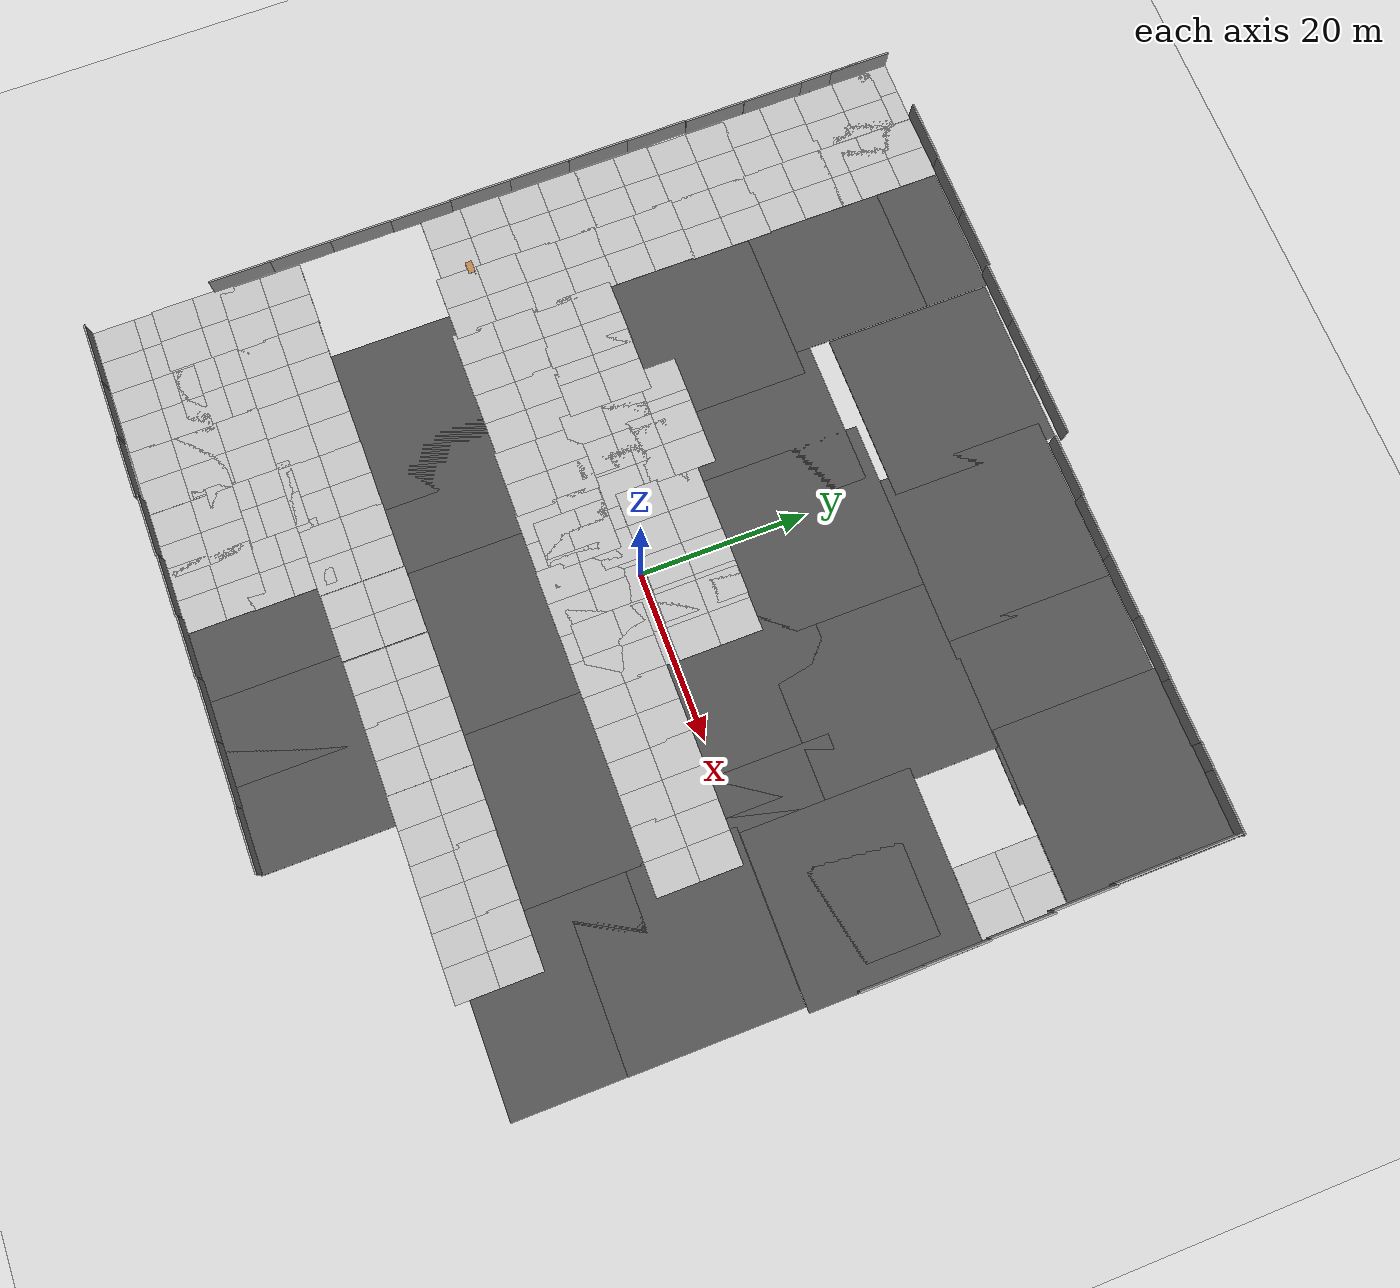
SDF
<sdf version="1.6">
 <world name="default">
  <light name="sun" type="directional">
   <pose>0 0 10 0 -0 0</pose>
   <diffuse>0.8 0.8 0.8 1</diffuse>
   <specular>0.2 0.2 0.2 1</specular>
   <attenuation>
    <range>1000</range>
    <constant>0.9</constant>
    <linear>0.01</linear>
    <quadratic>0.001</quadratic>
   </attenuation>
   <direction>-0.5 0.1 -0.9</direction>
  </light>
  <model name="ground_plane">
   <static>1</static>
   <link name="link">
    <collision name="collision">
     <geometry><plane><normal>0 0 1</normal><size>100 100</size></plane></geometry>
     <surface><friction><ode><mu>100</mu><mu2>50</mu2></ode></friction></surface>
    </collision>
    <visual name="visual">
     <cast_shadows>0</cast_shadows>
     <geometry><plane><normal>0 0 1</normal><size>100 100</size></plane></geometry>
     <material>
      <script><uri>file://media/materials/scripts/gazebo.material</uri><name>Gazebo/Grey</name></script>
     </material>
    </visual>
   </link>
  </model>
  <gravity>0 0 -9.8</gravity>
  <magnetic_field>6e-06 2.3e-05 -4.2e-05</magnetic_field>
  <atmosphere type="adiabatic"/>
  <physics name="default_physics" default="0" type="ode">
   <max_step_size>0.001</max_step_size>
   <real_time_factor>1</real_time_factor>
   <real_time_update_rate>1000</real_time_update_rate>
  </physics>
  <scene><ambient>0.4 0.4 0.4 1</ambient><background>0.7 0.7 0.7 1</background><shadows>1</shadows></scene>
  <spherical_coordinates>
   <surface_model>EARTH_WGS84</surface_model>
   <latitude_deg>0</latitude_deg>
   <longitude_deg>0</longitude_deg>
   <elevation>0</elevation>
   <heading_deg>0</heading_deg>
  </spherical_coordinates>
  <model name="mud_box">
   <static>1</static>
   <link name="link">
    <collision name="collision"><geometry><box><size>8 10 0.2</size></box></geometry></collision>
    <visual name="visual_1">
     <pose>-2 2.5 0 0 -0 0</pose>
     <cast_shadows>0</cast_shadows>
     <geometry><box><size>4 5 0.2</size></box></geometry>
     <material>
      <script>
       <uri>model://mud_box/materials/scripts</uri>
       <uri>model://mud_box/materials/textures</uri>
       <name>vrc/mud</name>
      </script>
     </material>
    </visual>
    <visual name="visual_2">
     <pose>2 2.5 0 0 -0 0</pose>
     <cast_shadows>0</cast_shadows>
     <geometry><box><size>4 5 0.2</size></box></geometry>
     <material>
      <script>
       <uri>model://mud_box/materials/scripts</uri>
       <uri>model://mud_box/materials/textures</uri>
       <name>vrc/mud</name>
      </script>
     </material>
    </visual>
    <visual name="visual_3">
     <pose>2 -2.5 0 0 -0 0</pose>
     <cast_shadows>0</cast_shadows>
     <geometry><box><size>4 5 0.2</size></box></geometry>
     <material>
      <script>
       <uri>model://mud_box/materials/scripts</uri>
       <uri>model://mud_box/materials/textures</uri>
       <name>vrc/mud</name>
      </script>
     </material>
    </visual>
    <visual name="visual_4">
     <pose>-2 -2.5 0 0 -0 0</pose>
     <cast_shadows>0</cast_shadows>
     <geometry><box><size>4 5 0.2</size></box></geometry>
     <material>
      <script>
       <uri>model://mud_box/materials/scripts</uri>
       <uri>model://mud_box/materials/textures</uri>
       <name>vrc/mud</name>
      </script>
     </material>
    </visual>
   </link>
   <pose>6.67494 -4.37805 0 0 -0 0</pose>
  </model>
  <model name="mud_box_0">
   <static>1</static>
   <link name="link">
    <collision name="collision"><geometry><box><size>8 10 0.2</size></box></geometry></collision>
    <visual name="visual_1">
     <pose>-2 2.5 0 0 -0 0</pose>
     <cast_shadows>0</cast_shadows>
     <geometry><box><size>4 5 0.2</size></box></geometry>
     <material>
      <script>
       <uri>model://mud_box/materials/scripts</uri>
       <uri>model://mud_box/materials/textures</uri>
       <name>vrc/mud</name>
      </script>
     </material>
    </visual>
    <visual name="visual_2">
     <pose>2 2.5 0 0 -0 0</pose>
     <cast_shadows>0</cast_shadows>
     <geometry><box><size>4 5 0.2</size></box></geometry>
     <material>
      <script>
       <uri>model://mud_box/materials/scripts</uri>
       <uri>model://mud_box/materials/textures</uri>
       <name>vrc/mud</name>
      </script>
     </material>
    </visual>
    <visual name="visual_3">
     <pose>2 -2.5 0 0 -0 0</pose>
     <cast_shadows>0</cast_shadows>
     <geometry><box><size>4 5 0.2</size></box></geometry>
     <material>
      <script>
       <uri>model://mud_box/materials/scripts</uri>
       <uri>model://mud_box/materials/textures</uri>
       <name>vrc/mud</name>
      </script>
     </material>
    </visual>
    <visual name="visual_4">
     <pose>-2 -2.5 0 0 -0 0</pose>
     <cast_shadows>0</cast_shadows>
     <geometry><box><size>4 5 0.2</size></box></geometry>
     <material>
      <script>
       <uri>model://mud_box/materials/scripts</uri>
       <uri>model://mud_box/materials/textures</uri>
       <name>vrc/mud</name>
      </script>
     </material>
    </visual>
   </link>
   <pose>-1.31413 -4.41998 0 0 -0 0</pose>
  </model>
  <model name="mud_box_1">
   <static>1</static>
   <link name="link">
    <collision name="collision"><geometry><box><size>8 10 0.2</size></box></geometry></collision>
    <visual name="visual_1">
     <pose>-2 2.5 0 0 -0 0</pose>
     <cast_shadows>0</cast_shadows>
     <geometry><box><size>4 5 0.2</size></box></geometry>
     <material>
      <script>
       <uri>model://mud_box/materials/scripts</uri>
       <uri>model://mud_box/materials/textures</uri>
       <name>vrc/mud</name>
      </script>
     </material>
    </visual>
    <visual name="visual_2">
     <pose>2 2.5 0 0 -0 0</pose>
     <cast_shadows>0</cast_shadows>
     <geometry><box><size>4 5 0.2</size></box></geometry>
     <material>
      <script>
       <uri>model://mud_box/materials/scripts</uri>
       <uri>model://mud_box/materials/textures</uri>
       <name>vrc/mud</name>
      </script>
     </material>
    </visual>
    <visual name="visual_3">
     <pose>2 -2.5 0 0 -0 0</pose>
     <cast_shadows>0</cast_shadows>
     <geometry><box><size>4 5 0.2</size></box></geometry>
     <material>
      <script>
       <uri>model://mud_box/materials/scripts</uri>
       <uri>model://mud_box/materials/textures</uri>
       <name>vrc/mud</name>
      </script>
     </material>
    </visual>
    <visual name="visual_4">
     <pose>-2 -2.5 0 0 -0 0</pose>
     <cast_shadows>0</cast_shadows>
     <geometry><box><size>4 5 0.2</size></box></geometry>
     <material>
      <script>
       <uri>model://mud_box/materials/scripts</uri>
       <uri>model://mud_box/materials/textures</uri>
       <name>vrc/mud</name>
      </script>
     </material>
    </visual>
   </link>
   <pose>-5.88435 -4.38735 0 0 -0 0</pose>
  </model>
  <model name="mud_box_2">
   <static>1</static>
   <link name="link">
    <collision name="collision"><geometry><box><size>8 10 0.2</size></box></geometry></collision>
    <visual name="visual_1">
     <pose>-2 2.5 0 0 -0 0</pose>
     <cast_shadows>0</cast_shadows>
     <geometry><box><size>4 5 0.2</size></box></geometry>
     <material>
      <script>
       <uri>model://mud_box/materials/scripts</uri>
       <uri>model://mud_box/materials/textures</uri>
       <name>vrc/mud</name>
      </script>
     </material>
    </visual>
    <visual name="visual_2">
     <pose>2 2.5 0 0 -0 0</pose>
     <cast_shadows>0</cast_shadows>
     <geometry><box><size>4 5 0.2</size></box></geometry>
     <material>
      <script>
       <uri>model://mud_box/materials/scripts</uri>
       <uri>model://mud_box/materials/textures</uri>
       <name>vrc/mud</name>
      </script>
     </material>
    </visual>
    <visual name="visual_3">
     <pose>2 -2.5 0 0 -0 0</pose>
     <cast_shadows>0</cast_shadows>
     <geometry><box><size>4 5 0.2</size></box></geometry>
     <material>
      <script>
       <uri>model://mud_box/materials/scripts</uri>
       <uri>model://mud_box/materials/textures</uri>
       <name>vrc/mud</name>
      </script>
     </material>
    </visual>
    <visual name="visual_4">
     <pose>-2 -2.5 0 0 -0 0</pose>
     <cast_shadows>0</cast_shadows>
     <geometry><box><size>4 5 0.2</size></box></geometry>
     <material>
      <script>
       <uri>model://mud_box/materials/scripts</uri>
       <uri>model://mud_box/materials/textures</uri>
       <name>vrc/mud</name>
      </script>
     </material>
    </visual>
   </link>
   <pose>-5.85929 5.62111 0 0 -0 0</pose>
  </model>
  <model name="mud_box_3">
   <static>1</static>
   <link name="link">
    <collision name="collision"><geometry><box><size>8 10 0.2</size></box></geometry></collision>
    <visual name="visual_1">
     <pose>-2 2.5 0 0 -0 0</pose>
     <cast_shadows>0</cast_shadows>
     <geometry><box><size>4 5 0.2</size></box></geometry>
     <material>
      <script>
       <uri>model://mud_box/materials/scripts</uri>
       <uri>model://mud_box/materials/textures</uri>
       <name>vrc/mud</name>
      </script>
     </material>
    </visual>
    <visual name="visual_2">
     <pose>2 2.5 0 0 -0 0</pose>
     <cast_shadows>0</cast_shadows>
     <geometry><box><size>4 5 0.2</size></box></geometry>
     <material>
      <script>
       <uri>model://mud_box/materials/scripts</uri>
       <uri>model://mud_box/materials/textures</uri>
       <name>vrc/mud</name>
      </script>
     </material>
    </visual>
    <visual name="visual_3">
     <pose>2 -2.5 0 0 -0 0</pose>
     <cast_shadows>0</cast_shadows>
     <geometry><box><size>4 5 0.2</size></box></geometry>
     <material>
      <script>
       <uri>model://mud_box/materials/scripts</uri>
       <uri>model://mud_box/materials/textures</uri>
       <name>vrc/mud</name>
      </script>
     </material>
    </visual>
    <visual name="visual_4">
     <pose>-2 -2.5 0 0 -0 0</pose>
     <cast_shadows>0</cast_shadows>
     <geometry><box><size>4 5 0.2</size></box></geometry>
     <material>
      <script>
       <uri>model://mud_box/materials/scripts</uri>
       <uri>model://mud_box/materials/textures</uri>
       <name>vrc/mud</name>
      </script>
     </material>
    </visual>
   </link>
   <pose>2.11138 5.6492 0 0 -0 0</pose>
  </model>
  <model name="mud_box_4">
   <static>1</static>
   <link name="link">
    <collision name="collision"><geometry><box><size>8 10 0.2</size></box></geometry></collision>
    <visual name="visual_1">
     <pose>-2 2.5 0 0 -0 0</pose>
     <cast_shadows>0</cast_shadows>
     <geometry><box><size>4 5 0.2</size></box></geometry>
     <material>
      <script>
       <uri>model://mud_box/materials/scripts</uri>
       <uri>model://mud_box/materials/textures</uri>
       <name>vrc/mud</name>
      </script>
     </material>
    </visual>
    <visual name="visual_2">
     <pose>2 2.5 0 0 -0 0</pose>
     <cast_shadows>0</cast_shadows>
     <geometry><box><size>4 5 0.2</size></box></geometry>
     <material>
      <script>
       <uri>model://mud_box/materials/scripts</uri>
       <uri>model://mud_box/materials/textures</uri>
       <name>vrc/mud</name>
      </script>
     </material>
    </visual>
    <visual name="visual_3">
     <pose>2 -2.5 0 0 -0 0</pose>
     <cast_shadows>0</cast_shadows>
     <geometry><box><size>4 5 0.2</size></box></geometry>
     <material>
      <script>
       <uri>model://mud_box/materials/scripts</uri>
       <uri>model://mud_box/materials/textures</uri>
       <name>vrc/mud</name>
      </script>
     </material>
    </visual>
    <visual name="visual_4">
     <pose>-2 -2.5 0 0 -0 0</pose>
     <cast_shadows>0</cast_shadows>
     <geometry><box><size>4 5 0.2</size></box></geometry>
     <material>
      <script>
       <uri>model://mud_box/materials/scripts</uri>
       <uri>model://mud_box/materials/textures</uri>
       <name>vrc/mud</name>
      </script>
     </material>
    </visual>
   </link>
   <pose>6.7262 5.5782 0 0 -0 0</pose>
  </model>
  <model name="asphalt_plane">
   <static>1</static>
   <link name="link">
    <collision name="collision"><geometry><box><size>20 20 0.1</size></box></geometry></collision>
    <visual name="visual">
     <cast_shadows>0</cast_shadows>
     <geometry><box><size>20 20 0.1</size></box></geometry>
     <material>
      <script>
       <uri>model://asphalt_plane/materials/scripts</uri>
       <uri>model://asphalt_plane/materials/textures</uri>
       <name>vrc/asphalt</name>
      </script>
     </material>
    </visual>
   </link>
   <pose>0.46329 -19.4958 0 0 -0 0</pose>
  </model>
  <model name="asphalt_plane_0">
   <static>1</static>
   <link name="link">
    <collision name="collision"><geometry><box><size>20 20 0.1</size></box></geometry></collision>
    <visual name="visual">
     <cast_shadows>0</cast_shadows>
     <geometry><box><size>20 20 0.1</size></box></geometry>
     <material>
      <script>
       <uri>model://asphalt_plane/materials/scripts</uri>
       <uri>model://asphalt_plane/materials/textures</uri>
       <name>vrc/asphalt</name>
      </script>
     </material>
    </visual>
   </link>
   <pose>-19.3509 -19.4595 0 0 -0 0</pose>
  </model>
  <model name="asphalt_plane_1">
   <static>1</static>
   <link name="link">
    <collision name="collision"><geometry><box><size>20 20 0.1</size></box></geometry></collision>
    <visual name="visual">
     <cast_shadows>0</cast_shadows>
     <geometry><box><size>20 20 0.1</size></box></geometry>
     <material>
      <script>
       <uri>model://asphalt_plane/materials/scripts</uri>
       <uri>model://asphalt_plane/materials/textures</uri>
       <name>vrc/asphalt</name>
      </script>
     </material>
    </visual>
   </link>
   <pose>20.1586 -19.4171 0 0 -0 0</pose>
  </model>
  <model name="asphalt_plane_2">
   <static>1</static>
   <link name="link">
    <collision name="collision"><geometry><box><size>20 20 0.1</size></box></geometry></collision>
    <visual name="visual">
     <cast_shadows>0</cast_shadows>
     <geometry><box><size>20 20 0.1</size></box></geometry>
     <material>
      <script>
       <uri>model://asphalt_plane/materials/scripts</uri>
       <uri>model://asphalt_plane/materials/textures</uri>
       <name>vrc/asphalt</name>
      </script>
     </material>
    </visual>
   </link>
   <pose>-27.35 -19.5085 0 0 -0 0</pose>
  </model>
  <model name="mud_box_2_clone">
   <static>1</static>
   <link name="link">
    <collision name="collision"><geometry><box><size>8 10 0.2</size></box></geometry></collision>
    <visual name="visual_1">
     <pose>-2 2.5 0 0 -0 0</pose>
     <cast_shadows>0</cast_shadows>
     <geometry><box><size>4 5 0.2</size></box></geometry>
     <material>
      <script>
       <uri>model://mud_box/materials/scripts</uri>
       <uri>model://mud_box/materials/textures</uri>
       <name>vrc/mud</name>
      </script>
     </material>
    </visual>
    <visual name="visual_2">
     <pose>2 2.5 0 0 -0 0</pose>
     <cast_shadows>0</cast_shadows>
     <geometry><box><size>4 5 0.2</size></box></geometry>
     <material>
      <script>
       <uri>model://mud_box/materials/scripts</uri>
       <uri>model://mud_box/materials/textures</uri>
       <name>vrc/mud</name>
      </script>
     </material>
    </visual>
    <visual name="visual_3">
     <pose>2 -2.5 0 0 -0 0</pose>
     <cast_shadows>0</cast_shadows>
     <geometry><box><size>4 5 0.2</size></box></geometry>
     <material>
      <script>
       <uri>model://mud_box/materials/scripts</uri>
       <uri>model://mud_box/materials/textures</uri>
       <name>vrc/mud</name>
      </script>
     </material>
    </visual>
    <visual name="visual_4">
     <pose>-2 -2.5 0 0 -0 0</pose>
     <cast_shadows>0</cast_shadows>
     <geometry><box><size>4 5 0.2</size></box></geometry>
     <material>
      <script>
       <uri>model://mud_box/materials/scripts</uri>
       <uri>model://mud_box/materials/textures</uri>
       <name>vrc/mud</name>
      </script>
     </material>
    </visual>
   </link>
   <pose>-6.29821 -29.5881 0 0 -0 0</pose>
  </model>
  <model name="mud_box_2_clone_0">
   <static>1</static>
   <link name="link">
    <collision name="collision"><geometry><box><size>8 10 0.2</size></box></geometry></collision>
    <visual name="visual_1">
     <pose>-2 2.5 0 0 -0 0</pose>
     <cast_shadows>0</cast_shadows>
     <geometry><box><size>4 5 0.2</size></box></geometry>
     <material>
      <script>
       <uri>model://mud_box/materials/scripts</uri>
       <uri>model://mud_box/materials/textures</uri>
       <name>vrc/mud</name>
      </script>
     </material>
    </visual>
    <visual name="visual_2">
     <pose>2 2.5 0 0 -0 0</pose>
     <cast_shadows>0</cast_shadows>
     <geometry><box><size>4 5 0.2</size></box></geometry>
     <material>
      <script>
       <uri>model://mud_box/materials/scripts</uri>
       <uri>model://mud_box/materials/textures</uri>
       <name>vrc/mud</name>
      </script>
     </material>
    </visual>
    <visual name="visual_3">
     <pose>2 -2.5 0 0 -0 0</pose>
     <cast_shadows>0</cast_shadows>
     <geometry><box><size>4 5 0.2</size></box></geometry>
     <material>
      <script>
       <uri>model://mud_box/materials/scripts</uri>
       <uri>model://mud_box/materials/textures</uri>
       <name>vrc/mud</name>
      </script>
     </material>
    </visual>
    <visual name="visual_4">
     <pose>-2 -2.5 0 0 -0 0</pose>
     <cast_shadows>0</cast_shadows>
     <geometry><box><size>4 5 0.2</size></box></geometry>
     <material>
      <script>
       <uri>model://mud_box/materials/scripts</uri>
       <uri>model://mud_box/materials/textures</uri>
       <name>vrc/mud</name>
      </script>
     </material>
    </visual>
   </link>
   <pose>1.80119 -29.5516 0 0 -0 0</pose>
  </model>
  <model name="mud_box_2_clone_1">
   <static>1</static>
   <link name="link">
    <collision name="collision"><geometry><box><size>8 10 0.2</size></box></geometry></collision>
    <visual name="visual_1">
     <pose>-2 2.5 0 0 -0 0</pose>
     <cast_shadows>0</cast_shadows>
     <geometry><box><size>4 5 0.2</size></box></geometry>
     <material>
      <script>
       <uri>model://mud_box/materials/scripts</uri>
       <uri>model://mud_box/materials/textures</uri>
       <name>vrc/mud</name>
      </script>
     </material>
    </visual>
    <visual name="visual_2">
     <pose>2 2.5 0 0 -0 0</pose>
     <cast_shadows>0</cast_shadows>
     <geometry><box><size>4 5 0.2</size></box></geometry>
     <material>
      <script>
       <uri>model://mud_box/materials/scripts</uri>
       <uri>model://mud_box/materials/textures</uri>
       <name>vrc/mud</name>
      </script>
     </material>
    </visual>
    <visual name="visual_3">
     <pose>2 -2.5 0 0 -0 0</pose>
     <cast_shadows>0</cast_shadows>
     <geometry><box><size>4 5 0.2</size></box></geometry>
     <material>
      <script>
       <uri>model://mud_box/materials/scripts</uri>
       <uri>model://mud_box/materials/textures</uri>
       <name>vrc/mud</name>
      </script>
     </material>
    </visual>
    <visual name="visual_4">
     <pose>-2 -2.5 0 0 -0 0</pose>
     <cast_shadows>0</cast_shadows>
     <geometry><box><size>4 5 0.2</size></box></geometry>
     <material>
      <script>
       <uri>model://mud_box/materials/scripts</uri>
       <uri>model://mud_box/materials/textures</uri>
       <name>vrc/mud</name>
      </script>
     </material>
    </visual>
   </link>
   <pose>9.52834 -29.56 0 0 -0 0</pose>
  </model>
  <model name="mud_box_2_clone_2">
   <static>1</static>
   <link name="link">
    <collision name="collision"><geometry><box><size>8 10 0.2</size></box></geometry></collision>
    <visual name="visual_1">
     <pose>-2 2.5 0 0 -0 0</pose>
     <cast_shadows>0</cast_shadows>
     <geometry><box><size>4 5 0.2</size></box></geometry>
     <material>
      <script>
       <uri>model://mud_box/materials/scripts</uri>
       <uri>model://mud_box/materials/textures</uri>
       <name>vrc/mud</name>
      </script>
     </material>
    </visual>
    <visual name="visual_2">
     <pose>2 2.5 0 0 -0 0</pose>
     <cast_shadows>0</cast_shadows>
     <geometry><box><size>4 5 0.2</size></box></geometry>
     <material>
      <script>
       <uri>model://mud_box/materials/scripts</uri>
       <uri>model://mud_box/materials/textures</uri>
       <name>vrc/mud</name>
      </script>
     </material>
    </visual>
    <visual name="visual_3">
     <pose>2 -2.5 0 0 -0 0</pose>
     <cast_shadows>0</cast_shadows>
     <geometry><box><size>4 5 0.2</size></box></geometry>
     <material>
      <script>
       <uri>model://mud_box/materials/scripts</uri>
       <uri>model://mud_box/materials/textures</uri>
       <name>vrc/mud</name>
      </script>
     </material>
    </visual>
    <visual name="visual_4">
     <pose>-2 -2.5 0 0 -0 0</pose>
     <cast_shadows>0</cast_shadows>
     <geometry><box><size>4 5 0.2</size></box></geometry>
     <material>
      <script>
       <uri>model://mud_box/materials/scripts</uri>
       <uri>model://mud_box/materials/textures</uri>
       <name>vrc/mud</name>
      </script>
     </material>
    </visual>
   </link>
   <pose>17.5411 -29.599 0 0 -0 0</pose>
  </model>
  <model name="mud_box_2_clone_3">
   <static>1</static>
   <link name="link">
    <collision name="collision"><geometry><box><size>8 10 0.2</size></box></geometry></collision>
    <visual name="visual_1">
     <pose>-2 2.5 0 0 -0 0</pose>
     <cast_shadows>0</cast_shadows>
     <geometry><box><size>4 5 0.2</size></box></geometry>
     <material>
      <script>
       <uri>model://mud_box/materials/scripts</uri>
       <uri>model://mud_box/materials/textures</uri>
       <name>vrc/mud</name>
      </script>
     </material>
    </visual>
    <visual name="visual_2">
     <pose>2 2.5 0 0 -0 0</pose>
     <cast_shadows>0</cast_shadows>
     <geometry><box><size>4 5 0.2</size></box></geometry>
     <material>
      <script>
       <uri>model://mud_box/materials/scripts</uri>
       <uri>model://mud_box/materials/textures</uri>
       <name>vrc/mud</name>
      </script>
     </material>
    </visual>
    <visual name="visual_3">
     <pose>2 -2.5 0 0 -0 0</pose>
     <cast_shadows>0</cast_shadows>
     <geometry><box><size>4 5 0.2</size></box></geometry>
     <material>
      <script>
       <uri>model://mud_box/materials/scripts</uri>
       <uri>model://mud_box/materials/textures</uri>
       <name>vrc/mud</name>
      </script>
     </material>
    </visual>
    <visual name="visual_4">
     <pose>-2 -2.5 0 0 -0 0</pose>
     <cast_shadows>0</cast_shadows>
     <geometry><box><size>4 5 0.2</size></box></geometry>
     <material>
      <script>
       <uri>model://mud_box/materials/scripts</uri>
       <uri>model://mud_box/materials/textures</uri>
       <name>vrc/mud</name>
      </script>
     </material>
    </visual>
   </link>
   <pose>25.0381 -29.645 0 0 -0 0</pose>
  </model>
  <model name="mud_box_2_clone_4">
   <static>1</static>
   <link name="link">
    <collision name="collision"><geometry><box><size>8 10 0.2</size></box></geometry></collision>
    <visual name="visual_1">
     <pose>-2 2.5 0 0 -0 0</pose>
     <cast_shadows>0</cast_shadows>
     <geometry><box><size>4 5 0.2</size></box></geometry>
     <material>
      <script>
       <uri>model://mud_box/materials/scripts</uri>
       <uri>model://mud_box/materials/textures</uri>
       <name>vrc/mud</name>
      </script>
     </material>
    </visual>
    <visual name="visual_2">
     <pose>2 2.5 0 0 -0 0</pose>
     <cast_shadows>0</cast_shadows>
     <geometry><box><size>4 5 0.2</size></box></geometry>
     <material>
      <script>
       <uri>model://mud_box/materials/scripts</uri>
       <uri>model://mud_box/materials/textures</uri>
       <name>vrc/mud</name>
      </script>
     </material>
    </visual>
    <visual name="visual_3">
     <pose>2 -2.5 0 0 -0 0</pose>
     <cast_shadows>0</cast_shadows>
     <geometry><box><size>4 5 0.2</size></box></geometry>
     <material>
      <script>
       <uri>model://mud_box/materials/scripts</uri>
       <uri>model://mud_box/materials/textures</uri>
       <name>vrc/mud</name>
      </script>
     </material>
    </visual>
    <visual name="visual_4">
     <pose>-2 -2.5 0 0 -0 0</pose>
     <cast_shadows>0</cast_shadows>
     <geometry><box><size>4 5 0.2</size></box></geometry>
     <material>
      <script>
       <uri>model://mud_box/materials/scripts</uri>
       <uri>model://mud_box/materials/textures</uri>
       <name>vrc/mud</name>
      </script>
     </material>
    </visual>
   </link>
   <pose>-14.3475 -29.6616 0 0 -0 0</pose>
  </model>
  <model name="mud_box_2_clone_5">
   <static>1</static>
   <link name="link">
    <collision name="collision"><geometry><box><size>8 10 0.2</size></box></geometry></collision>
    <visual name="visual_1">
     <pose>-2 2.5 0 0 -0 0</pose>
     <cast_shadows>0</cast_shadows>
     <geometry><box><size>4 5 0.2</size></box></geometry>
     <material>
      <script>
       <uri>model://mud_box/materials/scripts</uri>
       <uri>model://mud_box/materials/textures</uri>
       <name>vrc/mud</name>
      </script>
     </material>
    </visual>
    <visual name="visual_2">
     <pose>2 2.5 0 0 -0 0</pose>
     <cast_shadows>0</cast_shadows>
     <geometry><box><size>4 5 0.2</size></box></geometry>
     <material>
      <script>
       <uri>model://mud_box/materials/scripts</uri>
       <uri>model://mud_box/materials/textures</uri>
       <name>vrc/mud</name>
      </script>
     </material>
    </visual>
    <visual name="visual_3">
     <pose>2 -2.5 0 0 -0 0</pose>
     <cast_shadows>0</cast_shadows>
     <geometry><box><size>4 5 0.2</size></box></geometry>
     <material>
      <script>
       <uri>model://mud_box/materials/scripts</uri>
       <uri>model://mud_box/materials/textures</uri>
       <name>vrc/mud</name>
      </script>
     </material>
    </visual>
    <visual name="visual_4">
     <pose>-2 -2.5 0 0 -0 0</pose>
     <cast_shadows>0</cast_shadows>
     <geometry><box><size>4 5 0.2</size></box></geometry>
     <material>
      <script>
       <uri>model://mud_box/materials/scripts</uri>
       <uri>model://mud_box/materials/textures</uri>
       <name>vrc/mud</name>
      </script>
     </material>
    </visual>
   </link>
   <pose>-22.2418 -29.6822 0 0 -0 0</pose>
  </model>
  <model name="mud_box_2_clone_6">
   <static>1</static>
   <link name="link">
    <collision name="collision"><geometry><box><size>8 10 0.2</size></box></geometry></collision>
    <visual name="visual_1">
     <pose>-2 2.5 0 0 -0 0</pose>
     <cast_shadows>0</cast_shadows>
     <geometry><box><size>4 5 0.2</size></box></geometry>
     <material>
      <script>
       <uri>model://mud_box/materials/scripts</uri>
       <uri>model://mud_box/materials/textures</uri>
       <name>vrc/mud</name>
      </script>
     </material>
    </visual>
    <visual name="visual_2">
     <pose>2 2.5 0 0 -0 0</pose>
     <cast_shadows>0</cast_shadows>
     <geometry><box><size>4 5 0.2</size></box></geometry>
     <material>
      <script>
       <uri>model://mud_box/materials/scripts</uri>
       <uri>model://mud_box/materials/textures</uri>
       <name>vrc/mud</name>
      </script>
     </material>
    </visual>
    <visual name="visual_3">
     <pose>2 -2.5 0 0 -0 0</pose>
     <cast_shadows>0</cast_shadows>
     <geometry><box><size>4 5 0.2</size></box></geometry>
     <material>
      <script>
       <uri>model://mud_box/materials/scripts</uri>
       <uri>model://mud_box/materials/textures</uri>
       <name>vrc/mud</name>
      </script>
     </material>
    </visual>
    <visual name="visual_4">
     <pose>-2 -2.5 0 0 -0 0</pose>
     <cast_shadows>0</cast_shadows>
     <geometry><box><size>4 5 0.2</size></box></geometry>
     <material>
      <script>
       <uri>model://mud_box/materials/scripts</uri>
       <uri>model://mud_box/materials/textures</uri>
       <name>vrc/mud</name>
      </script>
     </material>
    </visual>
   </link>
   <pose>-30.175 -29.7222 0 0 -0 0</pose>
  </model>
  <model name="mud_box_2_clone_7">
   <static>1</static>
   <link name="link">
    <collision name="collision"><geometry><box><size>8 10 0.2</size></box></geometry></collision>
    <visual name="visual_1">
     <pose>-2 2.5 0 0 -0 0</pose>
     <cast_shadows>0</cast_shadows>
     <geometry><box><size>4 5 0.2</size></box></geometry>
     <material>
      <script>
       <uri>model://mud_box/materials/scripts</uri>
       <uri>model://mud_box/materials/textures</uri>
       <name>vrc/mud</name>
      </script>
     </material>
    </visual>
    <visual name="visual_2">
     <pose>2 2.5 0 0 -0 0</pose>
     <cast_shadows>0</cast_shadows>
     <geometry><box><size>4 5 0.2</size></box></geometry>
     <material>
      <script>
       <uri>model://mud_box/materials/scripts</uri>
       <uri>model://mud_box/materials/textures</uri>
       <name>vrc/mud</name>
      </script>
     </material>
    </visual>
    <visual name="visual_3">
     <pose>2 -2.5 0 0 -0 0</pose>
     <cast_shadows>0</cast_shadows>
     <geometry><box><size>4 5 0.2</size></box></geometry>
     <material>
      <script>
       <uri>model://mud_box/materials/scripts</uri>
       <uri>model://mud_box/materials/textures</uri>
       <name>vrc/mud</name>
      </script>
     </material>
    </visual>
    <visual name="visual_4">
     <pose>-2 -2.5 0 0 -0 0</pose>
     <cast_shadows>0</cast_shadows>
     <geometry><box><size>4 5 0.2</size></box></geometry>
     <material>
      <script>
       <uri>model://mud_box/materials/scripts</uri>
       <uri>model://mud_box/materials/textures</uri>
       <name>vrc/mud</name>
      </script>
     </material>
    </visual>
   </link>
   <pose>-38.1218 -29.7385 0 0 -0 0</pose>
  </model>
  <model name="mud_box_2_clone_8">
   <static>1</static>
   <link name="link">
    <collision name="collision"><geometry><box><size>8 10 0.2</size></box></geometry></collision>
    <visual name="visual_1">
     <pose>-2 2.5 0 0 -0 0</pose>
     <cast_shadows>0</cast_shadows>
     <geometry><box><size>4 5 0.2</size></box></geometry>
     <material>
      <script>
       <uri>model://mud_box/materials/scripts</uri>
       <uri>model://mud_box/materials/textures</uri>
       <name>vrc/mud</name>
      </script>
     </material>
    </visual>
    <visual name="visual_2">
     <pose>2 2.5 0 0 -0 0</pose>
     <cast_shadows>0</cast_shadows>
     <geometry><box><size>4 5 0.2</size></box></geometry>
     <material>
      <script>
       <uri>model://mud_box/materials/scripts</uri>
       <uri>model://mud_box/materials/textures</uri>
       <name>vrc/mud</name>
      </script>
     </material>
    </visual>
    <visual name="visual_3">
     <pose>2 -2.5 0 0 -0 0</pose>
     <cast_shadows>0</cast_shadows>
     <geometry><box><size>4 5 0.2</size></box></geometry>
     <material>
      <script>
       <uri>model://mud_box/materials/scripts</uri>
       <uri>model://mud_box/materials/textures</uri>
       <name>vrc/mud</name>
      </script>
     </material>
    </visual>
    <visual name="visual_4">
     <pose>-2 -2.5 0 0 -0 0</pose>
     <cast_shadows>0</cast_shadows>
     <geometry><box><size>4 5 0.2</size></box></geometry>
     <material>
      <script>
       <uri>model://mud_box/materials/scripts</uri>
       <uri>model://mud_box/materials/textures</uri>
       <name>vrc/mud</name>
      </script>
     </material>
    </visual>
   </link>
   <pose>32.8401 -29.6668 0 0 -0 0</pose>
  </model>
  <model name="mud_box_2_clone_9">
   <static>1</static>
   <link name="link">
    <collision name="collision"><geometry><box><size>8 10 0.2</size></box></geometry></collision>
    <visual name="visual_1">
     <pose>-2 2.5 0 0 -0 0</pose>
     <cast_shadows>0</cast_shadows>
     <geometry><box><size>4 5 0.2</size></box></geometry>
     <material>
      <script>
       <uri>model://mud_box/materials/scripts</uri>
       <uri>model://mud_box/materials/textures</uri>
       <name>vrc/mud</name>
      </script>
     </material>
    </visual>
    <visual name="visual_2">
     <pose>2 2.5 0 0 -0 0</pose>
     <cast_shadows>0</cast_shadows>
     <geometry><box><size>4 5 0.2</size></box></geometry>
     <material>
      <script>
       <uri>model://mud_box/materials/scripts</uri>
       <uri>model://mud_box/materials/textures</uri>
       <name>vrc/mud</name>
      </script>
     </material>
    </visual>
    <visual name="visual_3">
     <pose>2 -2.5 0 0 -0 0</pose>
     <cast_shadows>0</cast_shadows>
     <geometry><box><size>4 5 0.2</size></box></geometry>
     <material>
      <script>
       <uri>model://mud_box/materials/scripts</uri>
       <uri>model://mud_box/materials/textures</uri>
       <name>vrc/mud</name>
      </script>
     </material>
    </visual>
    <visual name="visual_4">
     <pose>-2 -2.5 0 0 -0 0</pose>
     <cast_shadows>0</cast_shadows>
     <geometry><box><size>4 5 0.2</size></box></geometry>
     <material>
      <script>
       <uri>model://mud_box/materials/scripts</uri>
       <uri>model://mud_box/materials/textures</uri>
       <name>vrc/mud</name>
      </script>
     </material>
    </visual>
   </link>
   <pose>6.94055 -5.96852 0 0 -0 0</pose>
  </model>
  <model name="mud_box_2_clone_10">
   <static>1</static>
   <link name="link">
    <collision name="collision"><geometry><box><size>8 10 0.2</size></box></geometry></collision>
    <visual name="visual_1">
     <pose>-2 2.5 0 0 -0 0</pose>
     <cast_shadows>0</cast_shadows>
     <geometry><box><size>4 5 0.2</size></box></geometry>
     <material>
      <script>
       <uri>model://mud_box/materials/scripts</uri>
       <uri>model://mud_box/materials/textures</uri>
       <name>vrc/mud</name>
      </script>
     </material>
    </visual>
    <visual name="visual_2">
     <pose>2 2.5 0 0 -0 0</pose>
     <cast_shadows>0</cast_shadows>
     <geometry><box><size>4 5 0.2</size></box></geometry>
     <material>
      <script>
       <uri>model://mud_box/materials/scripts</uri>
       <uri>model://mud_box/materials/textures</uri>
       <name>vrc/mud</name>
      </script>
     </material>
    </visual>
    <visual name="visual_3">
     <pose>2 -2.5 0 0 -0 0</pose>
     <cast_shadows>0</cast_shadows>
     <geometry><box><size>4 5 0.2</size></box></geometry>
     <material>
      <script>
       <uri>model://mud_box/materials/scripts</uri>
       <uri>model://mud_box/materials/textures</uri>
       <name>vrc/mud</name>
      </script>
     </material>
    </visual>
    <visual name="visual_4">
     <pose>-2 -2.5 0 0 -0 0</pose>
     <cast_shadows>0</cast_shadows>
     <geometry><box><size>4 5 0.2</size></box></geometry>
     <material>
      <script>
       <uri>model://mud_box/materials/scripts</uri>
       <uri>model://mud_box/materials/textures</uri>
       <name>vrc/mud</name>
      </script>
     </material>
    </visual>
   </link>
   <pose>-0.426662 -6.00251 0 0 -0 0</pose>
  </model>
  <model name="mud_box_2_clone_11">
   <static>1</static>
   <link name="link">
    <collision name="collision"><geometry><box><size>8 10 0.2</size></box></geometry></collision>
    <visual name="visual_1">
     <pose>-2 2.5 0 0 -0 0</pose>
     <cast_shadows>0</cast_shadows>
     <geometry><box><size>4 5 0.2</size></box></geometry>
     <material>
      <script>
       <uri>model://mud_box/materials/scripts</uri>
       <uri>model://mud_box/materials/textures</uri>
       <name>vrc/mud</name>
      </script>
     </material>
    </visual>
    <visual name="visual_2">
     <pose>2 2.5 0 0 -0 0</pose>
     <cast_shadows>0</cast_shadows>
     <geometry><box><size>4 5 0.2</size></box></geometry>
     <material>
      <script>
       <uri>model://mud_box/materials/scripts</uri>
       <uri>model://mud_box/materials/textures</uri>
       <name>vrc/mud</name>
      </script>
     </material>
    </visual>
    <visual name="visual_3">
     <pose>2 -2.5 0 0 -0 0</pose>
     <cast_shadows>0</cast_shadows>
     <geometry><box><size>4 5 0.2</size></box></geometry>
     <material>
      <script>
       <uri>model://mud_box/materials/scripts</uri>
       <uri>model://mud_box/materials/textures</uri>
       <name>vrc/mud</name>
      </script>
     </material>
    </visual>
    <visual name="visual_4">
     <pose>-2 -2.5 0 0 -0 0</pose>
     <cast_shadows>0</cast_shadows>
     <geometry><box><size>4 5 0.2</size></box></geometry>
     <material>
      <script>
       <uri>model://mud_box/materials/scripts</uri>
       <uri>model://mud_box/materials/textures</uri>
       <name>vrc/mud</name>
      </script>
     </material>
    </visual>
   </link>
   <pose>-7.76973 -5.92616 0 0 -0 0</pose>
  </model>
  <model name="mud_box_2_clone_12">
   <static>1</static>
   <link name="link">
    <collision name="collision"><geometry><box><size>8 10 0.2</size></box></geometry></collision>
    <visual name="visual_1">
     <pose>-2 2.5 0 0 -0 0</pose>
     <cast_shadows>0</cast_shadows>
     <geometry><box><size>4 5 0.2</size></box></geometry>
     <material>
      <script>
       <uri>model://mud_box/materials/scripts</uri>
       <uri>model://mud_box/materials/textures</uri>
       <name>vrc/mud</name>
      </script>
     </material>
    </visual>
    <visual name="visual_2">
     <pose>2 2.5 0 0 -0 0</pose>
     <cast_shadows>0</cast_shadows>
     <geometry><box><size>4 5 0.2</size></box></geometry>
     <material>
      <script>
       <uri>model://mud_box/materials/scripts</uri>
       <uri>model://mud_box/materials/textures</uri>
       <name>vrc/mud</name>
      </script>
     </material>
    </visual>
    <visual name="visual_3">
     <pose>2 -2.5 0 0 -0 0</pose>
     <cast_shadows>0</cast_shadows>
     <geometry><box><size>4 5 0.2</size></box></geometry>
     <material>
      <script>
       <uri>model://mud_box/materials/scripts</uri>
       <uri>model://mud_box/materials/textures</uri>
       <name>vrc/mud</name>
      </script>
     </material>
    </visual>
    <visual name="visual_4">
     <pose>-2 -2.5 0 0 -0 0</pose>
     <cast_shadows>0</cast_shadows>
     <geometry><box><size>4 5 0.2</size></box></geometry>
     <material>
      <script>
       <uri>model://mud_box/materials/scripts</uri>
       <uri>model://mud_box/materials/textures</uri>
       <name>vrc/mud</name>
      </script>
     </material>
    </visual>
   </link>
   <pose>14.6148 -5.9147 0 0 -0 0</pose>
  </model>
  <model name="mud_box_2_clone_13">
   <static>1</static>
   <link name="link">
    <collision name="collision"><geometry><box><size>8 10 0.2</size></box></geometry></collision>
    <visual name="visual_1">
     <pose>-2 2.5 0 0 -0 0</pose>
     <cast_shadows>0</cast_shadows>
     <geometry><box><size>4 5 0.2</size></box></geometry>
     <material>
      <script>
       <uri>model://mud_box/materials/scripts</uri>
       <uri>model://mud_box/materials/textures</uri>
       <name>vrc/mud</name>
      </script>
     </material>
    </visual>
    <visual name="visual_2">
     <pose>2 2.5 0 0 -0 0</pose>
     <cast_shadows>0</cast_shadows>
     <geometry><box><size>4 5 0.2</size></box></geometry>
     <material>
      <script>
       <uri>model://mud_box/materials/scripts</uri>
       <uri>model://mud_box/materials/textures</uri>
       <name>vrc/mud</name>
      </script>
     </material>
    </visual>
    <visual name="visual_3">
     <pose>2 -2.5 0 0 -0 0</pose>
     <cast_shadows>0</cast_shadows>
     <geometry><box><size>4 5 0.2</size></box></geometry>
     <material>
      <script>
       <uri>model://mud_box/materials/scripts</uri>
       <uri>model://mud_box/materials/textures</uri>
       <name>vrc/mud</name>
      </script>
     </material>
    </visual>
    <visual name="visual_4">
     <pose>-2 -2.5 0 0 -0 0</pose>
     <cast_shadows>0</cast_shadows>
     <geometry><box><size>4 5 0.2</size></box></geometry>
     <material>
      <script>
       <uri>model://mud_box/materials/scripts</uri>
       <uri>model://mud_box/materials/textures</uri>
       <name>vrc/mud</name>
      </script>
     </material>
    </visual>
   </link>
   <pose>22.3759 -5.90953 0 0 -0 0</pose>
  </model>
  <model name="mud_box_2_clone_14">
   <static>1</static>
   <link name="link">
    <collision name="collision"><geometry><box><size>8 10 0.2</size></box></geometry></collision>
    <visual name="visual_1">
     <pose>-2 2.5 0 0 -0 0</pose>
     <cast_shadows>0</cast_shadows>
     <geometry><box><size>4 5 0.2</size></box></geometry>
     <material>
      <script>
       <uri>model://mud_box/materials/scripts</uri>
       <uri>model://mud_box/materials/textures</uri>
       <name>vrc/mud</name>
      </script>
     </material>
    </visual>
    <visual name="visual_2">
     <pose>2 2.5 0 0 -0 0</pose>
     <cast_shadows>0</cast_shadows>
     <geometry><box><size>4 5 0.2</size></box></geometry>
     <material>
      <script>
       <uri>model://mud_box/materials/scripts</uri>
       <uri>model://mud_box/materials/textures</uri>
       <name>vrc/mud</name>
      </script>
     </material>
    </visual>
    <visual name="visual_3">
     <pose>2 -2.5 0 0 -0 0</pose>
     <cast_shadows>0</cast_shadows>
     <geometry><box><size>4 5 0.2</size></box></geometry>
     <material>
      <script>
       <uri>model://mud_box/materials/scripts</uri>
       <uri>model://mud_box/materials/textures</uri>
       <name>vrc/mud</name>
      </script>
     </material>
    </visual>
    <visual name="visual_4">
     <pose>-2 -2.5 0 0 -0 0</pose>
     <cast_shadows>0</cast_shadows>
     <geometry><box><size>4 5 0.2</size></box></geometry>
     <material>
      <script>
       <uri>model://mud_box/materials/scripts</uri>
       <uri>model://mud_box/materials/textures</uri>
       <name>vrc/mud</name>
      </script>
     </material>
    </visual>
   </link>
   <pose>29.9864 -5.92338 0 0 -0 0</pose>
  </model>
  <model name="mud_box_2_clone_15">
   <static>1</static>
   <link name="link">
    <collision name="collision"><geometry><box><size>8 10 0.2</size></box></geometry></collision>
    <visual name="visual_1">
     <pose>-2 2.5 0 0 -0 0</pose>
     <cast_shadows>0</cast_shadows>
     <geometry><box><size>4 5 0.2</size></box></geometry>
     <material>
      <script>
       <uri>model://mud_box/materials/scripts</uri>
       <uri>model://mud_box/materials/textures</uri>
       <name>vrc/mud</name>
      </script>
     </material>
    </visual>
    <visual name="visual_2">
     <pose>2 2.5 0 0 -0 0</pose>
     <cast_shadows>0</cast_shadows>
     <geometry><box><size>4 5 0.2</size></box></geometry>
     <material>
      <script>
       <uri>model://mud_box/materials/scripts</uri>
       <uri>model://mud_box/materials/textures</uri>
       <name>vrc/mud</name>
      </script>
     </material>
    </visual>
    <visual name="visual_3">
     <pose>2 -2.5 0 0 -0 0</pose>
     <cast_shadows>0</cast_shadows>
     <geometry><box><size>4 5 0.2</size></box></geometry>
     <material>
      <script>
       <uri>model://mud_box/materials/scripts</uri>
       <uri>model://mud_box/materials/textures</uri>
       <name>vrc/mud</name>
      </script>
     </material>
    </visual>
    <visual name="visual_4">
     <pose>-2 -2.5 0 0 -0 0</pose>
     <cast_shadows>0</cast_shadows>
     <geometry><box><size>4 5 0.2</size></box></geometry>
     <material>
      <script>
       <uri>model://mud_box/materials/scripts</uri>
       <uri>model://mud_box/materials/textures</uri>
       <name>vrc/mud</name>
      </script>
     </material>
    </visual>
   </link>
   <pose>-15.3121 -5.76558 0 0 -0 0</pose>
  </model>
  <model name="mud_box_2_clone_16">
   <static>1</static>
   <link name="link">
    <collision name="collision"><geometry><box><size>8 10 0.2</size></box></geometry></collision>
    <visual name="visual_1">
     <pose>-2 2.5 0 0 -0 0</pose>
     <cast_shadows>0</cast_shadows>
     <geometry><box><size>4 5 0.2</size></box></geometry>
     <material>
      <script>
       <uri>model://mud_box/materials/scripts</uri>
       <uri>model://mud_box/materials/textures</uri>
       <name>vrc/mud</name>
      </script>
     </material>
    </visual>
    <visual name="visual_2">
     <pose>2 2.5 0 0 -0 0</pose>
     <cast_shadows>0</cast_shadows>
     <geometry><box><size>4 5 0.2</size></box></geometry>
     <material>
      <script>
       <uri>model://mud_box/materials/scripts</uri>
       <uri>model://mud_box/materials/textures</uri>
       <name>vrc/mud</name>
      </script>
     </material>
    </visual>
    <visual name="visual_3">
     <pose>2 -2.5 0 0 -0 0</pose>
     <cast_shadows>0</cast_shadows>
     <geometry><box><size>4 5 0.2</size></box></geometry>
     <material>
      <script>
       <uri>model://mud_box/materials/scripts</uri>
       <uri>model://mud_box/materials/textures</uri>
       <name>vrc/mud</name>
      </script>
     </material>
    </visual>
    <visual name="visual_4">
     <pose>-2 -2.5 0 0 -0 0</pose>
     <cast_shadows>0</cast_shadows>
     <geometry><box><size>4 5 0.2</size></box></geometry>
     <material>
      <script>
       <uri>model://mud_box/materials/scripts</uri>
       <uri>model://mud_box/materials/textures</uri>
       <name>vrc/mud</name>
      </script>
     </material>
    </visual>
   </link>
   <pose>-23.1666 -5.5652 0 0 -0 0</pose>
  </model>
  <model name="mud_box_5">
   <static>1</static>
   <link name="link">
    <collision name="collision"><geometry><box><size>8 10 0.2</size></box></geometry></collision>
    <visual name="visual_1">
     <pose>-2 2.5 0 0 -0 0</pose>
     <cast_shadows>0</cast_shadows>
     <geometry><box><size>4 5 0.2</size></box></geometry>
     <material>
      <script>
       <uri>model://mud_box/materials/scripts</uri>
       <uri>model://mud_box/materials/textures</uri>
       <name>vrc/mud</name>
      </script>
     </material>
    </visual>
    <visual name="visual_2">
     <pose>2 2.5 0 0 -0 0</pose>
     <cast_shadows>0</cast_shadows>
     <geometry><box><size>4 5 0.2</size></box></geometry>
     <material>
      <script>
       <uri>model://mud_box/materials/scripts</uri>
       <uri>model://mud_box/materials/textures</uri>
       <name>vrc/mud</name>
      </script>
     </material>
    </visual>
    <visual name="visual_3">
     <pose>2 -2.5 0 0 -0 0</pose>
     <cast_shadows>0</cast_shadows>
     <geometry><box><size>4 5 0.2</size></box></geometry>
     <material>
      <script>
       <uri>model://mud_box/materials/scripts</uri>
       <uri>model://mud_box/materials/textures</uri>
       <name>vrc/mud</name>
      </script>
     </material>
    </visual>
    <visual name="visual_4">
     <pose>-2 -2.5 0 0 -0 0</pose>
     <cast_shadows>0</cast_shadows>
     <geometry><box><size>4 5 0.2</size></box></geometry>
     <material>
      <script>
       <uri>model://mud_box/materials/scripts</uri>
       <uri>model://mud_box/materials/textures</uri>
       <name>vrc/mud</name>
      </script>
     </material>
    </visual>
   </link>
   <pose>-30.8349 -5.5936 0 0 -0 0</pose>
  </model>
  <model name="mud_box_5_clone_0">
   <static>1</static>
   <link name="link">
    <collision name="collision"><geometry><box><size>8 10 0.2</size></box></geometry></collision>
    <visual name="visual_1">
     <pose>-2 2.5 0 0 -0 0</pose>
     <cast_shadows>0</cast_shadows>
     <geometry><box><size>4 5 0.2</size></box></geometry>
     <material>
      <script>
       <uri>model://mud_box/materials/scripts</uri>
       <uri>model://mud_box/materials/textures</uri>
       <name>vrc/mud</name>
      </script>
     </material>
    </visual>
    <visual name="visual_2">
     <pose>2 2.5 0 0 -0 0</pose>
     <cast_shadows>0</cast_shadows>
     <geometry><box><size>4 5 0.2</size></box></geometry>
     <material>
      <script>
       <uri>model://mud_box/materials/scripts</uri>
       <uri>model://mud_box/materials/textures</uri>
       <name>vrc/mud</name>
      </script>
     </material>
    </visual>
    <visual name="visual_3">
     <pose>2 -2.5 0 0 -0 0</pose>
     <cast_shadows>0</cast_shadows>
     <geometry><box><size>4 5 0.2</size></box></geometry>
     <material>
      <script>
       <uri>model://mud_box/materials/scripts</uri>
       <uri>model://mud_box/materials/textures</uri>
       <name>vrc/mud</name>
      </script>
     </material>
    </visual>
    <visual name="visual_4">
     <pose>-2 -2.5 0 0 -0 0</pose>
     <cast_shadows>0</cast_shadows>
     <geometry><box><size>4 5 0.2</size></box></geometry>
     <material>
      <script>
       <uri>model://mud_box/materials/scripts</uri>
       <uri>model://mud_box/materials/textures</uri>
       <name>vrc/mud</name>
      </script>
     </material>
    </visual>
   </link>
   <pose>-46.0429 -4.43965 0 0 -0 0</pose>
  </model>
  <model name="mud_box_5_clone_1">
   <static>1</static>
   <link name="link">
    <collision name="collision"><geometry><box><size>8 10 0.2</size></box></geometry></collision>
    <visual name="visual_1">
     <pose>-2 2.5 0 0 -0 0</pose>
     <cast_shadows>0</cast_shadows>
     <geometry><box><size>4 5 0.2</size></box></geometry>
     <material>
      <script>
       <uri>model://mud_box/materials/scripts</uri>
       <uri>model://mud_box/materials/textures</uri>
       <name>vrc/mud</name>
      </script>
     </material>
    </visual>
    <visual name="visual_2">
     <pose>2 2.5 0 0 -0 0</pose>
     <cast_shadows>0</cast_shadows>
     <geometry><box><size>4 5 0.2</size></box></geometry>
     <material>
      <script>
       <uri>model://mud_box/materials/scripts</uri>
       <uri>model://mud_box/materials/textures</uri>
       <name>vrc/mud</name>
      </script>
     </material>
    </visual>
    <visual name="visual_3">
     <pose>2 -2.5 0 0 -0 0</pose>
     <cast_shadows>0</cast_shadows>
     <geometry><box><size>4 5 0.2</size></box></geometry>
     <material>
      <script>
       <uri>model://mud_box/materials/scripts</uri>
       <uri>model://mud_box/materials/textures</uri>
       <name>vrc/mud</name>
      </script>
     </material>
    </visual>
    <visual name="visual_4">
     <pose>-2 -2.5 0 0 -0 0</pose>
     <cast_shadows>0</cast_shadows>
     <geometry><box><size>4 5 0.2</size></box></geometry>
     <material>
      <script>
       <uri>model://mud_box/materials/scripts</uri>
       <uri>model://mud_box/materials/textures</uri>
       <name>vrc/mud</name>
      </script>
     </material>
    </visual>
   </link>
   <pose>-45.9576 5.44414 0 0 -0 0</pose>
  </model>
  <model name="mud_box_5_clone_2">
   <static>1</static>
   <link name="link">
    <collision name="collision"><geometry><box><size>8 10 0.2</size></box></geometry></collision>
    <visual name="visual_1">
     <pose>-2 2.5 0 0 -0 0</pose>
     <cast_shadows>0</cast_shadows>
     <geometry><box><size>4 5 0.2</size></box></geometry>
     <material>
      <script>
       <uri>model://mud_box/materials/scripts</uri>
       <uri>model://mud_box/materials/textures</uri>
       <name>vrc/mud</name>
      </script>
     </material>
    </visual>
    <visual name="visual_2">
     <pose>2 2.5 0 0 -0 0</pose>
     <cast_shadows>0</cast_shadows>
     <geometry><box><size>4 5 0.2</size></box></geometry>
     <material>
      <script>
       <uri>model://mud_box/materials/scripts</uri>
       <uri>model://mud_box/materials/textures</uri>
       <name>vrc/mud</name>
      </script>
     </material>
    </visual>
    <visual name="visual_3">
     <pose>2 -2.5 0 0 -0 0</pose>
     <cast_shadows>0</cast_shadows>
     <geometry><box><size>4 5 0.2</size></box></geometry>
     <material>
      <script>
       <uri>model://mud_box/materials/scripts</uri>
       <uri>model://mud_box/materials/textures</uri>
       <name>vrc/mud</name>
      </script>
     </material>
    </visual>
    <visual name="visual_4">
     <pose>-2 -2.5 0 0 -0 0</pose>
     <cast_shadows>0</cast_shadows>
     <geometry><box><size>4 5 0.2</size></box></geometry>
     <material>
      <script>
       <uri>model://mud_box/materials/scripts</uri>
       <uri>model://mud_box/materials/textures</uri>
       <name>vrc/mud</name>
      </script>
     </material>
    </visual>
   </link>
   <pose>-38.1608 4.8659 0 0 -0 0</pose>
  </model>
  <model name="mud_box_5_clone_3">
   <static>1</static>
   <link name="link">
    <collision name="collision"><geometry><box><size>8 10 0.2</size></box></geometry></collision>
    <visual name="visual_1">
     <pose>-2 2.5 0 0 -0 0</pose>
     <cast_shadows>0</cast_shadows>
     <geometry><box><size>4 5 0.2</size></box></geometry>
     <material>
      <script>
       <uri>model://mud_box/materials/scripts</uri>
       <uri>model://mud_box/materials/textures</uri>
       <name>vrc/mud</name>
      </script>
     </material>
    </visual>
    <visual name="visual_2">
     <pose>2 2.5 0 0 -0 0</pose>
     <cast_shadows>0</cast_shadows>
     <geometry><box><size>4 5 0.2</size></box></geometry>
     <material>
      <script>
       <uri>model://mud_box/materials/scripts</uri>
       <uri>model://mud_box/materials/textures</uri>
       <name>vrc/mud</name>
      </script>
     </material>
    </visual>
    <visual name="visual_3">
     <pose>2 -2.5 0 0 -0 0</pose>
     <cast_shadows>0</cast_shadows>
     <geometry><box><size>4 5 0.2</size></box></geometry>
     <material>
      <script>
       <uri>model://mud_box/materials/scripts</uri>
       <uri>model://mud_box/materials/textures</uri>
       <name>vrc/mud</name>
      </script>
     </material>
    </visual>
    <visual name="visual_4">
     <pose>-2 -2.5 0 0 -0 0</pose>
     <cast_shadows>0</cast_shadows>
     <geometry><box><size>4 5 0.2</size></box></geometry>
     <material>
      <script>
       <uri>model://mud_box/materials/scripts</uri>
       <uri>model://mud_box/materials/textures</uri>
       <name>vrc/mud</name>
      </script>
     </material>
    </visual>
   </link>
   <pose>-30.8215 4.10783 0 0 -0 0</pose>
  </model>
  <model name="mud_box_5_clone_4">
   <static>1</static>
   <link name="link">
    <collision name="collision"><geometry><box><size>8 10 0.2</size></box></geometry></collision>
    <visual name="visual_1">
     <pose>-2 2.5 0 0 -0 0</pose>
     <cast_shadows>0</cast_shadows>
     <geometry><box><size>4 5 0.2</size></box></geometry>
     <material>
      <script>
       <uri>model://mud_box/materials/scripts</uri>
       <uri>model://mud_box/materials/textures</uri>
       <name>vrc/mud</name>
      </script>
     </material>
    </visual>
    <visual name="visual_2">
     <pose>2 2.5 0 0 -0 0</pose>
     <cast_shadows>0</cast_shadows>
     <geometry><box><size>4 5 0.2</size></box></geometry>
     <material>
      <script>
       <uri>model://mud_box/materials/scripts</uri>
       <uri>model://mud_box/materials/textures</uri>
       <name>vrc/mud</name>
      </script>
     </material>
    </visual>
    <visual name="visual_3">
     <pose>2 -2.5 0 0 -0 0</pose>
     <cast_shadows>0</cast_shadows>
     <geometry><box><size>4 5 0.2</size></box></geometry>
     <material>
      <script>
       <uri>model://mud_box/materials/scripts</uri>
       <uri>model://mud_box/materials/textures</uri>
       <name>vrc/mud</name>
      </script>
     </material>
    </visual>
    <visual name="visual_4">
     <pose>-2 -2.5 0 0 -0 0</pose>
     <cast_shadows>0</cast_shadows>
     <geometry><box><size>4 5 0.2</size></box></geometry>
     <material>
      <script>
       <uri>model://mud_box/materials/scripts</uri>
       <uri>model://mud_box/materials/textures</uri>
       <name>vrc/mud</name>
      </script>
     </material>
    </visual>
   </link>
   <pose>-24.5157 4.05379 0 0 -0 0</pose>
  </model>
  <model name="mud_box_5_clone_1_clone">
   <static>1</static>
   <link name="link">
    <collision name="collision"><geometry><box><size>8 10 0.2</size></box></geometry></collision>
    <visual name="visual_1">
     <pose>-2 2.5 0 0 -0 0</pose>
     <cast_shadows>0</cast_shadows>
     <geometry><box><size>4 5 0.2</size></box></geometry>
     <material>
      <script>
       <uri>model://mud_box/materials/scripts</uri>
       <uri>model://mud_box/materials/textures</uri>
       <name>vrc/mud</name>
      </script>
     </material>
    </visual>
    <visual name="visual_2">
     <pose>2 2.5 0 0 -0 0</pose>
     <cast_shadows>0</cast_shadows>
     <geometry><box><size>4 5 0.2</size></box></geometry>
     <material>
      <script>
       <uri>model://mud_box/materials/scripts</uri>
       <uri>model://mud_box/materials/textures</uri>
       <name>vrc/mud</name>
      </script>
     </material>
    </visual>
    <visual name="visual_3">
     <pose>2 -2.5 0 0 -0 0</pose>
     <cast_shadows>0</cast_shadows>
     <geometry><box><size>4 5 0.2</size></box></geometry>
     <material>
      <script>
       <uri>model://mud_box/materials/scripts</uri>
       <uri>model://mud_box/materials/textures</uri>
       <name>vrc/mud</name>
      </script>
     </material>
    </visual>
    <visual name="visual_4">
     <pose>-2 -2.5 0 0 -0 0</pose>
     <cast_shadows>0</cast_shadows>
     <geometry><box><size>4 5 0.2</size></box></geometry>
     <material>
      <script>
       <uri>model://mud_box/materials/scripts</uri>
       <uri>model://mud_box/materials/textures</uri>
       <name>vrc/mud</name>
      </script>
     </material>
    </visual>
   </link>
   <pose>-45.9289 15.1657 0 0 -0 0</pose>
  </model>
  <model name="mud_box_5_clone_1_clone_0">
   <static>1</static>
   <link name="link">
    <collision name="collision"><geometry><box><size>8 10 0.2</size></box></geometry></collision>
    <visual name="visual_1">
     <pose>-2 2.5 0 0 -0 0</pose>
     <cast_shadows>0</cast_shadows>
     <geometry><box><size>4 5 0.2</size></box></geometry>
     <material>
      <script>
       <uri>model://mud_box/materials/scripts</uri>
       <uri>model://mud_box/materials/textures</uri>
       <name>vrc/mud</name>
      </script>
     </material>
    </visual>
    <visual name="visual_2">
     <pose>2 2.5 0 0 -0 0</pose>
     <cast_shadows>0</cast_shadows>
     <geometry><box><size>4 5 0.2</size></box></geometry>
     <material>
      <script>
       <uri>model://mud_box/materials/scripts</uri>
       <uri>model://mud_box/materials/textures</uri>
       <name>vrc/mud</name>
      </script>
     </material>
    </visual>
    <visual name="visual_3">
     <pose>2 -2.5 0 0 -0 0</pose>
     <cast_shadows>0</cast_shadows>
     <geometry><box><size>4 5 0.2</size></box></geometry>
     <material>
      <script>
       <uri>model://mud_box/materials/scripts</uri>
       <uri>model://mud_box/materials/textures</uri>
       <name>vrc/mud</name>
      </script>
     </material>
    </visual>
    <visual name="visual_4">
     <pose>-2 -2.5 0 0 -0 0</pose>
     <cast_shadows>0</cast_shadows>
     <geometry><box><size>4 5 0.2</size></box></geometry>
     <material>
      <script>
       <uri>model://mud_box/materials/scripts</uri>
       <uri>model://mud_box/materials/textures</uri>
       <name>vrc/mud</name>
      </script>
     </material>
    </visual>
   </link>
   <pose>-38.1705 14.7563 0 0 -0 0</pose>
  </model>
  <model name="mud_box_5_clone_1_clone_1">
   <static>1</static>
   <link name="link">
    <collision name="collision"><geometry><box><size>8 10 0.2</size></box></geometry></collision>
    <visual name="visual_1">
     <pose>-2 2.5 0 0 -0 0</pose>
     <cast_shadows>0</cast_shadows>
     <geometry><box><size>4 5 0.2</size></box></geometry>
     <material>
      <script>
       <uri>model://mud_box/materials/scripts</uri>
       <uri>model://mud_box/materials/textures</uri>
       <name>vrc/mud</name>
      </script>
     </material>
    </visual>
    <visual name="visual_2">
     <pose>2 2.5 0 0 -0 0</pose>
     <cast_shadows>0</cast_shadows>
     <geometry><box><size>4 5 0.2</size></box></geometry>
     <material>
      <script>
       <uri>model://mud_box/materials/scripts</uri>
       <uri>model://mud_box/materials/textures</uri>
       <name>vrc/mud</name>
      </script>
     </material>
    </visual>
    <visual name="visual_3">
     <pose>2 -2.5 0 0 -0 0</pose>
     <cast_shadows>0</cast_shadows>
     <geometry><box><size>4 5 0.2</size></box></geometry>
     <material>
      <script>
       <uri>model://mud_box/materials/scripts</uri>
       <uri>model://mud_box/materials/textures</uri>
       <name>vrc/mud</name>
      </script>
     </material>
    </visual>
    <visual name="visual_4">
     <pose>-2 -2.5 0 0 -0 0</pose>
     <cast_shadows>0</cast_shadows>
     <geometry><box><size>4 5 0.2</size></box></geometry>
     <material>
      <script>
       <uri>model://mud_box/materials/scripts</uri>
       <uri>model://mud_box/materials/textures</uri>
       <name>vrc/mud</name>
      </script>
     </material>
    </visual>
   </link>
   <pose>-38.0105 24.5085 0 0 -0 0</pose>
  </model>
  <model name="mud_box_5_clone_1_clone_2">
   <static>1</static>
   <link name="link">
    <collision name="collision"><geometry><box><size>8 10 0.2</size></box></geometry></collision>
    <visual name="visual_1">
     <pose>-2 2.5 0 0 -0 0</pose>
     <cast_shadows>0</cast_shadows>
     <geometry><box><size>4 5 0.2</size></box></geometry>
     <material>
      <script>
       <uri>model://mud_box/materials/scripts</uri>
       <uri>model://mud_box/materials/textures</uri>
       <name>vrc/mud</name>
      </script>
     </material>
    </visual>
    <visual name="visual_2">
     <pose>2 2.5 0 0 -0 0</pose>
     <cast_shadows>0</cast_shadows>
     <geometry><box><size>4 5 0.2</size></box></geometry>
     <material>
      <script>
       <uri>model://mud_box/materials/scripts</uri>
       <uri>model://mud_box/materials/textures</uri>
       <name>vrc/mud</name>
      </script>
     </material>
    </visual>
    <visual name="visual_3">
     <pose>2 -2.5 0 0 -0 0</pose>
     <cast_shadows>0</cast_shadows>
     <geometry><box><size>4 5 0.2</size></box></geometry>
     <material>
      <script>
       <uri>model://mud_box/materials/scripts</uri>
       <uri>model://mud_box/materials/textures</uri>
       <name>vrc/mud</name>
      </script>
     </material>
    </visual>
    <visual name="visual_4">
     <pose>-2 -2.5 0 0 -0 0</pose>
     <cast_shadows>0</cast_shadows>
     <geometry><box><size>4 5 0.2</size></box></geometry>
     <material>
      <script>
       <uri>model://mud_box/materials/scripts</uri>
       <uri>model://mud_box/materials/textures</uri>
       <name>vrc/mud</name>
      </script>
     </material>
    </visual>
   </link>
   <pose>-45.8143 24.5123 0 0 -0 0</pose>
  </model>
  <model name="mud_box_5_clone_1_clone_3">
   <static>1</static>
   <link name="link">
    <collision name="collision"><geometry><box><size>8 10 0.2</size></box></geometry></collision>
    <visual name="visual_1">
     <pose>-2 2.5 0 0 -0 0</pose>
     <cast_shadows>0</cast_shadows>
     <geometry><box><size>4 5 0.2</size></box></geometry>
     <material>
      <script>
       <uri>model://mud_box/materials/scripts</uri>
       <uri>model://mud_box/materials/textures</uri>
       <name>vrc/mud</name>
      </script>
     </material>
    </visual>
    <visual name="visual_2">
     <pose>2 2.5 0 0 -0 0</pose>
     <cast_shadows>0</cast_shadows>
     <geometry><box><size>4 5 0.2</size></box></geometry>
     <material>
      <script>
       <uri>model://mud_box/materials/scripts</uri>
       <uri>model://mud_box/materials/textures</uri>
       <name>vrc/mud</name>
      </script>
     </material>
    </visual>
    <visual name="visual_3">
     <pose>2 -2.5 0 0 -0 0</pose>
     <cast_shadows>0</cast_shadows>
     <geometry><box><size>4 5 0.2</size></box></geometry>
     <material>
      <script>
       <uri>model://mud_box/materials/scripts</uri>
       <uri>model://mud_box/materials/textures</uri>
       <name>vrc/mud</name>
      </script>
     </material>
    </visual>
    <visual name="visual_4">
     <pose>-2 -2.5 0 0 -0 0</pose>
     <cast_shadows>0</cast_shadows>
     <geometry><box><size>4 5 0.2</size></box></geometry>
     <material>
      <script>
       <uri>model://mud_box/materials/scripts</uri>
       <uri>model://mud_box/materials/textures</uri>
       <name>vrc/mud</name>
      </script>
     </material>
    </visual>
   </link>
   <pose>-46.0438 34.2972 0 0 -0 0</pose>
  </model>
  <model name="mud_box_5_clone_1_clone_4">
   <static>1</static>
   <link name="link">
    <collision name="collision"><geometry><box><size>8 10 0.2</size></box></geometry></collision>
    <visual name="visual_1">
     <pose>-2 2.5 0 0 -0 0</pose>
     <cast_shadows>0</cast_shadows>
     <geometry><box><size>4 5 0.2</size></box></geometry>
     <material>
      <script>
       <uri>model://mud_box/materials/scripts</uri>
       <uri>model://mud_box/materials/textures</uri>
       <name>vrc/mud</name>
      </script>
     </material>
    </visual>
    <visual name="visual_2">
     <pose>2 2.5 0 0 -0 0</pose>
     <cast_shadows>0</cast_shadows>
     <geometry><box><size>4 5 0.2</size></box></geometry>
     <material>
      <script>
       <uri>model://mud_box/materials/scripts</uri>
       <uri>model://mud_box/materials/textures</uri>
       <name>vrc/mud</name>
      </script>
     </material>
    </visual>
    <visual name="visual_3">
     <pose>2 -2.5 0 0 -0 0</pose>
     <cast_shadows>0</cast_shadows>
     <geometry><box><size>4 5 0.2</size></box></geometry>
     <material>
      <script>
       <uri>model://mud_box/materials/scripts</uri>
       <uri>model://mud_box/materials/textures</uri>
       <name>vrc/mud</name>
      </script>
     </material>
    </visual>
    <visual name="visual_4">
     <pose>-2 -2.5 0 0 -0 0</pose>
     <cast_shadows>0</cast_shadows>
     <geometry><box><size>4 5 0.2</size></box></geometry>
     <material>
      <script>
       <uri>model://mud_box/materials/scripts</uri>
       <uri>model://mud_box/materials/textures</uri>
       <name>vrc/mud</name>
      </script>
     </material>
    </visual>
   </link>
   <pose>-38.1404 34.0458 0 0 -0 0</pose>
  </model>
  <model name="mud_box_5_clone_1_clone_5">
   <static>1</static>
   <link name="link">
    <collision name="collision"><geometry><box><size>8 10 0.2</size></box></geometry></collision>
    <visual name="visual_1">
     <pose>-2 2.5 0 0 -0 0</pose>
     <cast_shadows>0</cast_shadows>
     <geometry><box><size>4 5 0.2</size></box></geometry>
     <material>
      <script>
       <uri>model://mud_box/materials/scripts</uri>
       <uri>model://mud_box/materials/textures</uri>
       <name>vrc/mud</name>
      </script>
     </material>
    </visual>
    <visual name="visual_2">
     <pose>2 2.5 0 0 -0 0</pose>
     <cast_shadows>0</cast_shadows>
     <geometry><box><size>4 5 0.2</size></box></geometry>
     <material>
      <script>
       <uri>model://mud_box/materials/scripts</uri>
       <uri>model://mud_box/materials/textures</uri>
       <name>vrc/mud</name>
      </script>
     </material>
    </visual>
    <visual name="visual_3">
     <pose>2 -2.5 0 0 -0 0</pose>
     <cast_shadows>0</cast_shadows>
     <geometry><box><size>4 5 0.2</size></box></geometry>
     <material>
      <script>
       <uri>model://mud_box/materials/scripts</uri>
       <uri>model://mud_box/materials/textures</uri>
       <name>vrc/mud</name>
      </script>
     </material>
    </visual>
    <visual name="visual_4">
     <pose>-2 -2.5 0 0 -0 0</pose>
     <cast_shadows>0</cast_shadows>
     <geometry><box><size>4 5 0.2</size></box></geometry>
     <material>
      <script>
       <uri>model://mud_box/materials/scripts</uri>
       <uri>model://mud_box/materials/textures</uri>
       <name>vrc/mud</name>
      </script>
     </material>
    </visual>
   </link>
   <pose>-38.1282 43.8196 0 0 -0 0</pose>
  </model>
  <model name="mud_box_5_clone_1_clone_6">
   <static>1</static>
   <link name="link">
    <collision name="collision"><geometry><box><size>8 10 0.2</size></box></geometry></collision>
    <visual name="visual_1">
     <pose>-2 2.5 0 0 -0 0</pose>
     <cast_shadows>0</cast_shadows>
     <geometry><box><size>4 5 0.2</size></box></geometry>
     <material>
      <script>
       <uri>model://mud_box/materials/scripts</uri>
       <uri>model://mud_box/materials/textures</uri>
       <name>vrc/mud</name>
      </script>
     </material>
    </visual>
    <visual name="visual_2">
     <pose>2 2.5 0 0 -0 0</pose>
     <cast_shadows>0</cast_shadows>
     <geometry><box><size>4 5 0.2</size></box></geometry>
     <material>
      <script>
       <uri>model://mud_box/materials/scripts</uri>
       <uri>model://mud_box/materials/textures</uri>
       <name>vrc/mud</name>
      </script>
     </material>
    </visual>
    <visual name="visual_3">
     <pose>2 -2.5 0 0 -0 0</pose>
     <cast_shadows>0</cast_shadows>
     <geometry><box><size>4 5 0.2</size></box></geometry>
     <material>
      <script>
       <uri>model://mud_box/materials/scripts</uri>
       <uri>model://mud_box/materials/textures</uri>
       <name>vrc/mud</name>
      </script>
     </material>
    </visual>
    <visual name="visual_4">
     <pose>-2 -2.5 0 0 -0 0</pose>
     <cast_shadows>0</cast_shadows>
     <geometry><box><size>4 5 0.2</size></box></geometry>
     <material>
      <script>
       <uri>model://mud_box/materials/scripts</uri>
       <uri>model://mud_box/materials/textures</uri>
       <name>vrc/mud</name>
      </script>
     </material>
    </visual>
   </link>
   <pose>-45.8976 43.8224 0 0 -0 0</pose>
  </model>
  <model name="mud_box_5_clone_1_clone_7">
   <static>1</static>
   <link name="link">
    <collision name="collision"><geometry><box><size>8 10 0.2</size></box></geometry></collision>
    <visual name="visual_1">
     <pose>-2 2.5 0 0 -0 0</pose>
     <cast_shadows>0</cast_shadows>
     <geometry><box><size>4 5 0.2</size></box></geometry>
     <material>
      <script>
       <uri>model://mud_box/materials/scripts</uri>
       <uri>model://mud_box/materials/textures</uri>
       <name>vrc/mud</name>
      </script>
     </material>
    </visual>
    <visual name="visual_2">
     <pose>2 2.5 0 0 -0 0</pose>
     <cast_shadows>0</cast_shadows>
     <geometry><box><size>4 5 0.2</size></box></geometry>
     <material>
      <script>
       <uri>model://mud_box/materials/scripts</uri>
       <uri>model://mud_box/materials/textures</uri>
       <name>vrc/mud</name>
      </script>
     </material>
    </visual>
    <visual name="visual_3">
     <pose>2 -2.5 0 0 -0 0</pose>
     <cast_shadows>0</cast_shadows>
     <geometry><box><size>4 5 0.2</size></box></geometry>
     <material>
      <script>
       <uri>model://mud_box/materials/scripts</uri>
       <uri>model://mud_box/materials/textures</uri>
       <name>vrc/mud</name>
      </script>
     </material>
    </visual>
    <visual name="visual_4">
     <pose>-2 -2.5 0 0 -0 0</pose>
     <cast_shadows>0</cast_shadows>
     <geometry><box><size>4 5 0.2</size></box></geometry>
     <material>
      <script>
       <uri>model://mud_box/materials/scripts</uri>
       <uri>model://mud_box/materials/textures</uri>
       <name>vrc/mud</name>
      </script>
     </material>
    </visual>
   </link>
   <pose>-46.1676 46.0228 0 0 -0 0</pose>
  </model>
  <model name="mud_box_5_clone_1_clone_8">
   <static>1</static>
   <link name="link">
    <collision name="collision"><geometry><box><size>8 10 0.2</size></box></geometry></collision>
    <visual name="visual_1">
     <pose>-2 2.5 0 0 -0 0</pose>
     <cast_shadows>0</cast_shadows>
     <geometry><box><size>4 5 0.2</size></box></geometry>
     <material>
      <script>
       <uri>model://mud_box/materials/scripts</uri>
       <uri>model://mud_box/materials/textures</uri>
       <name>vrc/mud</name>
      </script>
     </material>
    </visual>
    <visual name="visual_2">
     <pose>2 2.5 0 0 -0 0</pose>
     <cast_shadows>0</cast_shadows>
     <geometry><box><size>4 5 0.2</size></box></geometry>
     <material>
      <script>
       <uri>model://mud_box/materials/scripts</uri>
       <uri>model://mud_box/materials/textures</uri>
       <name>vrc/mud</name>
      </script>
     </material>
    </visual>
    <visual name="visual_3">
     <pose>2 -2.5 0 0 -0 0</pose>
     <cast_shadows>0</cast_shadows>
     <geometry><box><size>4 5 0.2</size></box></geometry>
     <material>
      <script>
       <uri>model://mud_box/materials/scripts</uri>
       <uri>model://mud_box/materials/textures</uri>
       <name>vrc/mud</name>
      </script>
     </material>
    </visual>
    <visual name="visual_4">
     <pose>-2 -2.5 0 0 -0 0</pose>
     <cast_shadows>0</cast_shadows>
     <geometry><box><size>4 5 0.2</size></box></geometry>
     <material>
      <script>
       <uri>model://mud_box/materials/scripts</uri>
       <uri>model://mud_box/materials/textures</uri>
       <name>vrc/mud</name>
      </script>
     </material>
    </visual>
   </link>
   <pose>-38.1143 46.3826 0 0 -0 0</pose>
  </model>
  <model name="mud_box_5_clone_1_clone_4_clone">
   <static>1</static>
   <link name="link">
    <collision name="collision"><geometry><box><size>8 10 0.2</size></box></geometry></collision>
    <visual name="visual_1">
     <pose>-2 2.5 0 0 -0 0</pose>
     <cast_shadows>0</cast_shadows>
     <geometry><box><size>4 5 0.2</size></box></geometry>
     <material>
      <script>
       <uri>model://mud_box/materials/scripts</uri>
       <uri>model://mud_box/materials/textures</uri>
       <name>vrc/mud</name>
      </script>
     </material>
    </visual>
    <visual name="visual_2">
     <pose>2 2.5 0 0 -0 0</pose>
     <cast_shadows>0</cast_shadows>
     <geometry><box><size>4 5 0.2</size></box></geometry>
     <material>
      <script>
       <uri>model://mud_box/materials/scripts</uri>
       <uri>model://mud_box/materials/textures</uri>
       <name>vrc/mud</name>
      </script>
     </material>
    </visual>
    <visual name="visual_3">
     <pose>2 -2.5 0 0 -0 0</pose>
     <cast_shadows>0</cast_shadows>
     <geometry><box><size>4 5 0.2</size></box></geometry>
     <material>
      <script>
       <uri>model://mud_box/materials/scripts</uri>
       <uri>model://mud_box/materials/textures</uri>
       <name>vrc/mud</name>
      </script>
     </material>
    </visual>
    <visual name="visual_4">
     <pose>-2 -2.5 0 0 -0 0</pose>
     <cast_shadows>0</cast_shadows>
     <geometry><box><size>4 5 0.2</size></box></geometry>
     <material>
      <script>
       <uri>model://mud_box/materials/scripts</uri>
       <uri>model://mud_box/materials/textures</uri>
       <name>vrc/mud</name>
      </script>
     </material>
    </visual>
   </link>
   <pose>-45.8606 -29.6589 0 0 -0 0</pose>
  </model>
  <model name="mud_box_5_clone_1_clone_4_clone_clone">
   <static>1</static>
   <link name="link">
    <collision name="collision"><geometry><box><size>8 10 0.2</size></box></geometry></collision>
    <visual name="visual_1">
     <pose>-2 2.5 0 0 -0 0</pose>
     <cast_shadows>0</cast_shadows>
     <geometry><box><size>4 5 0.2</size></box></geometry>
     <material>
      <script>
       <uri>model://mud_box/materials/scripts</uri>
       <uri>model://mud_box/materials/textures</uri>
       <name>vrc/mud</name>
      </script>
     </material>
    </visual>
    <visual name="visual_2">
     <pose>2 2.5 0 0 -0 0</pose>
     <cast_shadows>0</cast_shadows>
     <geometry><box><size>4 5 0.2</size></box></geometry>
     <material>
      <script>
       <uri>model://mud_box/materials/scripts</uri>
       <uri>model://mud_box/materials/textures</uri>
       <name>vrc/mud</name>
      </script>
     </material>
    </visual>
    <visual name="visual_3">
     <pose>2 -2.5 0 0 -0 0</pose>
     <cast_shadows>0</cast_shadows>
     <geometry><box><size>4 5 0.2</size></box></geometry>
     <material>
      <script>
       <uri>model://mud_box/materials/scripts</uri>
       <uri>model://mud_box/materials/textures</uri>
       <name>vrc/mud</name>
      </script>
     </material>
    </visual>
    <visual name="visual_4">
     <pose>-2 -2.5 0 0 -0 0</pose>
     <cast_shadows>0</cast_shadows>
     <geometry><box><size>4 5 0.2</size></box></geometry>
     <material>
      <script>
       <uri>model://mud_box/materials/scripts</uri>
       <uri>model://mud_box/materials/textures</uri>
       <name>vrc/mud</name>
      </script>
     </material>
    </visual>
   </link>
   <pose>-45.9664 -45.0649 0 0 -0 0</pose>
  </model>
  <model name="mud_box_5_clone_1_clone_4_clone_clone_0">
   <static>1</static>
   <link name="link">
    <collision name="collision"><geometry><box><size>8 10 0.2</size></box></geometry></collision>
    <visual name="visual_1">
     <pose>-2 2.5 0 0 -0 0</pose>
     <cast_shadows>0</cast_shadows>
     <geometry><box><size>4 5 0.2</size></box></geometry>
     <material>
      <script>
       <uri>model://mud_box/materials/scripts</uri>
       <uri>model://mud_box/materials/textures</uri>
       <name>vrc/mud</name>
      </script>
     </material>
    </visual>
    <visual name="visual_2">
     <pose>2 2.5 0 0 -0 0</pose>
     <cast_shadows>0</cast_shadows>
     <geometry><box><size>4 5 0.2</size></box></geometry>
     <material>
      <script>
       <uri>model://mud_box/materials/scripts</uri>
       <uri>model://mud_box/materials/textures</uri>
       <name>vrc/mud</name>
      </script>
     </material>
    </visual>
    <visual name="visual_3">
     <pose>2 -2.5 0 0 -0 0</pose>
     <cast_shadows>0</cast_shadows>
     <geometry><box><size>4 5 0.2</size></box></geometry>
     <material>
      <script>
       <uri>model://mud_box/materials/scripts</uri>
       <uri>model://mud_box/materials/textures</uri>
       <name>vrc/mud</name>
      </script>
     </material>
    </visual>
    <visual name="visual_4">
     <pose>-2 -2.5 0 0 -0 0</pose>
     <cast_shadows>0</cast_shadows>
     <geometry><box><size>4 5 0.2</size></box></geometry>
     <material>
      <script>
       <uri>model://mud_box/materials/scripts</uri>
       <uri>model://mud_box/materials/textures</uri>
       <name>vrc/mud</name>
      </script>
     </material>
    </visual>
   </link>
   <pose>-46.1763 -37.8638 0 0 -0 0</pose>
  </model>
  <model name="mud_box_5_clone_1_clone_4_clone_clone_1">
   <static>1</static>
   <link name="link">
    <collision name="collision"><geometry><box><size>8 10 0.2</size></box></geometry></collision>
    <visual name="visual_1">
     <pose>-2 2.5 0 0 -0 0</pose>
     <cast_shadows>0</cast_shadows>
     <geometry><box><size>4 5 0.2</size></box></geometry>
     <material>
      <script>
       <uri>model://mud_box/materials/scripts</uri>
       <uri>model://mud_box/materials/textures</uri>
       <name>vrc/mud</name>
      </script>
     </material>
    </visual>
    <visual name="visual_2">
     <pose>2 2.5 0 0 -0 0</pose>
     <cast_shadows>0</cast_shadows>
     <geometry><box><size>4 5 0.2</size></box></geometry>
     <material>
      <script>
       <uri>model://mud_box/materials/scripts</uri>
       <uri>model://mud_box/materials/textures</uri>
       <name>vrc/mud</name>
      </script>
     </material>
    </visual>
    <visual name="visual_3">
     <pose>2 -2.5 0 0 -0 0</pose>
     <cast_shadows>0</cast_shadows>
     <geometry><box><size>4 5 0.2</size></box></geometry>
     <material>
      <script>
       <uri>model://mud_box/materials/scripts</uri>
       <uri>model://mud_box/materials/textures</uri>
       <name>vrc/mud</name>
      </script>
     </material>
    </visual>
    <visual name="visual_4">
     <pose>-2 -2.5 0 0 -0 0</pose>
     <cast_shadows>0</cast_shadows>
     <geometry><box><size>4 5 0.2</size></box></geometry>
     <material>
      <script>
       <uri>model://mud_box/materials/scripts</uri>
       <uri>model://mud_box/materials/textures</uri>
       <name>vrc/mud</name>
      </script>
     </material>
    </visual>
   </link>
   <pose>-38.0528 -45.0636 0 0 -0 0</pose>
  </model>
  <model name="mud_box_5_clone_1_clone_4_clone_clone_2">
   <static>1</static>
   <link name="link">
    <collision name="collision"><geometry><box><size>8 10 0.2</size></box></geometry></collision>
    <visual name="visual_1">
     <pose>-2 2.5 0 0 -0 0</pose>
     <cast_shadows>0</cast_shadows>
     <geometry><box><size>4 5 0.2</size></box></geometry>
     <material>
      <script>
       <uri>model://mud_box/materials/scripts</uri>
       <uri>model://mud_box/materials/textures</uri>
       <name>vrc/mud</name>
      </script>
     </material>
    </visual>
    <visual name="visual_2">
     <pose>2 2.5 0 0 -0 0</pose>
     <cast_shadows>0</cast_shadows>
     <geometry><box><size>4 5 0.2</size></box></geometry>
     <material>
      <script>
       <uri>model://mud_box/materials/scripts</uri>
       <uri>model://mud_box/materials/textures</uri>
       <name>vrc/mud</name>
      </script>
     </material>
    </visual>
    <visual name="visual_3">
     <pose>2 -2.5 0 0 -0 0</pose>
     <cast_shadows>0</cast_shadows>
     <geometry><box><size>4 5 0.2</size></box></geometry>
     <material>
      <script>
       <uri>model://mud_box/materials/scripts</uri>
       <uri>model://mud_box/materials/textures</uri>
       <name>vrc/mud</name>
      </script>
     </material>
    </visual>
    <visual name="visual_4">
     <pose>-2 -2.5 0 0 -0 0</pose>
     <cast_shadows>0</cast_shadows>
     <geometry><box><size>4 5 0.2</size></box></geometry>
     <material>
      <script>
       <uri>model://mud_box/materials/scripts</uri>
       <uri>model://mud_box/materials/textures</uri>
       <name>vrc/mud</name>
      </script>
     </material>
    </visual>
   </link>
   <pose>-38.2366 -37.6293 0 0 -0 0</pose>
  </model>
  <model name="mud_box_5_clone_1_clone_4_clone_clone_3">
   <static>1</static>
   <link name="link">
    <collision name="collision"><geometry><box><size>8 10 0.2</size></box></geometry></collision>
    <visual name="visual_1">
     <pose>-2 2.5 0 0 -0 0</pose>
     <cast_shadows>0</cast_shadows>
     <geometry><box><size>4 5 0.2</size></box></geometry>
     <material>
      <script>
       <uri>model://mud_box/materials/scripts</uri>
       <uri>model://mud_box/materials/textures</uri>
       <name>vrc/mud</name>
      </script>
     </material>
    </visual>
    <visual name="visual_2">
     <pose>2 2.5 0 0 -0 0</pose>
     <cast_shadows>0</cast_shadows>
     <geometry><box><size>4 5 0.2</size></box></geometry>
     <material>
      <script>
       <uri>model://mud_box/materials/scripts</uri>
       <uri>model://mud_box/materials/textures</uri>
       <name>vrc/mud</name>
      </script>
     </material>
    </visual>
    <visual name="visual_3">
     <pose>2 -2.5 0 0 -0 0</pose>
     <cast_shadows>0</cast_shadows>
     <geometry><box><size>4 5 0.2</size></box></geometry>
     <material>
      <script>
       <uri>model://mud_box/materials/scripts</uri>
       <uri>model://mud_box/materials/textures</uri>
       <name>vrc/mud</name>
      </script>
     </material>
    </visual>
    <visual name="visual_4">
     <pose>-2 -2.5 0 0 -0 0</pose>
     <cast_shadows>0</cast_shadows>
     <geometry><box><size>4 5 0.2</size></box></geometry>
     <material>
      <script>
       <uri>model://mud_box/materials/scripts</uri>
       <uri>model://mud_box/materials/textures</uri>
       <name>vrc/mud</name>
      </script>
     </material>
    </visual>
   </link>
   <pose>-30.3951 -39.6922 0 0 -0 0</pose>
  </model>
  <model name="mud_box_5_clone_1_clone_4_clone_clone_4">
   <static>1</static>
   <link name="link">
    <collision name="collision"><geometry><box><size>8 10 0.2</size></box></geometry></collision>
    <visual name="visual_1">
     <pose>-2 2.5 0 0 -0 0</pose>
     <cast_shadows>0</cast_shadows>
     <geometry><box><size>4 5 0.2</size></box></geometry>
     <material>
      <script>
       <uri>model://mud_box/materials/scripts</uri>
       <uri>model://mud_box/materials/textures</uri>
       <name>vrc/mud</name>
      </script>
     </material>
    </visual>
    <visual name="visual_2">
     <pose>2 2.5 0 0 -0 0</pose>
     <cast_shadows>0</cast_shadows>
     <geometry><box><size>4 5 0.2</size></box></geometry>
     <material>
      <script>
       <uri>model://mud_box/materials/scripts</uri>
       <uri>model://mud_box/materials/textures</uri>
       <name>vrc/mud</name>
      </script>
     </material>
    </visual>
    <visual name="visual_3">
     <pose>2 -2.5 0 0 -0 0</pose>
     <cast_shadows>0</cast_shadows>
     <geometry><box><size>4 5 0.2</size></box></geometry>
     <material>
      <script>
       <uri>model://mud_box/materials/scripts</uri>
       <uri>model://mud_box/materials/textures</uri>
       <name>vrc/mud</name>
      </script>
     </material>
    </visual>
    <visual name="visual_4">
     <pose>-2 -2.5 0 0 -0 0</pose>
     <cast_shadows>0</cast_shadows>
     <geometry><box><size>4 5 0.2</size></box></geometry>
     <material>
      <script>
       <uri>model://mud_box/materials/scripts</uri>
       <uri>model://mud_box/materials/textures</uri>
       <name>vrc/mud</name>
      </script>
     </material>
    </visual>
   </link>
   <pose>-30.2135 -45.0793 0 0 -0 0</pose>
  </model>
  <model name="mud_box_5_clone_1_clone_4_clone_clone_5">
   <static>1</static>
   <link name="link">
    <collision name="collision"><geometry><box><size>8 10 0.2</size></box></geometry></collision>
    <visual name="visual_1">
     <pose>-2 2.5 0 0 -0 0</pose>
     <cast_shadows>0</cast_shadows>
     <geometry><box><size>4 5 0.2</size></box></geometry>
     <material>
      <script>
       <uri>model://mud_box/materials/scripts</uri>
       <uri>model://mud_box/materials/textures</uri>
       <name>vrc/mud</name>
      </script>
     </material>
    </visual>
    <visual name="visual_2">
     <pose>2 2.5 0 0 -0 0</pose>
     <cast_shadows>0</cast_shadows>
     <geometry><box><size>4 5 0.2</size></box></geometry>
     <material>
      <script>
       <uri>model://mud_box/materials/scripts</uri>
       <uri>model://mud_box/materials/textures</uri>
       <name>vrc/mud</name>
      </script>
     </material>
    </visual>
    <visual name="visual_3">
     <pose>2 -2.5 0 0 -0 0</pose>
     <cast_shadows>0</cast_shadows>
     <geometry><box><size>4 5 0.2</size></box></geometry>
     <material>
      <script>
       <uri>model://mud_box/materials/scripts</uri>
       <uri>model://mud_box/materials/textures</uri>
       <name>vrc/mud</name>
      </script>
     </material>
    </visual>
    <visual name="visual_4">
     <pose>-2 -2.5 0 0 -0 0</pose>
     <cast_shadows>0</cast_shadows>
     <geometry><box><size>4 5 0.2</size></box></geometry>
     <material>
      <script>
       <uri>model://mud_box/materials/scripts</uri>
       <uri>model://mud_box/materials/textures</uri>
       <name>vrc/mud</name>
      </script>
     </material>
    </visual>
   </link>
   <pose>-22.1912 -45.095 0 0 -0 0</pose>
  </model>
  <model name="mud_box_5_clone_1_clone_4_clone_clone_6">
   <static>1</static>
   <link name="link">
    <collision name="collision"><geometry><box><size>8 10 0.2</size></box></geometry></collision>
    <visual name="visual_1">
     <pose>-2 2.5 0 0 -0 0</pose>
     <cast_shadows>0</cast_shadows>
     <geometry><box><size>4 5 0.2</size></box></geometry>
     <material>
      <script>
       <uri>model://mud_box/materials/scripts</uri>
       <uri>model://mud_box/materials/textures</uri>
       <name>vrc/mud</name>
      </script>
     </material>
    </visual>
    <visual name="visual_2">
     <pose>2 2.5 0 0 -0 0</pose>
     <cast_shadows>0</cast_shadows>
     <geometry><box><size>4 5 0.2</size></box></geometry>
     <material>
      <script>
       <uri>model://mud_box/materials/scripts</uri>
       <uri>model://mud_box/materials/textures</uri>
       <name>vrc/mud</name>
      </script>
     </material>
    </visual>
    <visual name="visual_3">
     <pose>2 -2.5 0 0 -0 0</pose>
     <cast_shadows>0</cast_shadows>
     <geometry><box><size>4 5 0.2</size></box></geometry>
     <material>
      <script>
       <uri>model://mud_box/materials/scripts</uri>
       <uri>model://mud_box/materials/textures</uri>
       <name>vrc/mud</name>
      </script>
     </material>
    </visual>
    <visual name="visual_4">
     <pose>-2 -2.5 0 0 -0 0</pose>
     <cast_shadows>0</cast_shadows>
     <geometry><box><size>4 5 0.2</size></box></geometry>
     <material>
      <script>
       <uri>model://mud_box/materials/scripts</uri>
       <uri>model://mud_box/materials/textures</uri>
       <name>vrc/mud</name>
      </script>
     </material>
    </visual>
   </link>
   <pose>-22.986 -38.1709 0 0 -0 0</pose>
  </model>
  <model name="mud_box_5_clone_1_clone_4_clone_clone_7">
   <static>1</static>
   <link name="link">
    <collision name="collision"><geometry><box><size>8 10 0.2</size></box></geometry></collision>
    <visual name="visual_1">
     <pose>-2 2.5 0 0 -0 0</pose>
     <cast_shadows>0</cast_shadows>
     <geometry><box><size>4 5 0.2</size></box></geometry>
     <material>
      <script>
       <uri>model://mud_box/materials/scripts</uri>
       <uri>model://mud_box/materials/textures</uri>
       <name>vrc/mud</name>
      </script>
     </material>
    </visual>
    <visual name="visual_2">
     <pose>2 2.5 0 0 -0 0</pose>
     <cast_shadows>0</cast_shadows>
     <geometry><box><size>4 5 0.2</size></box></geometry>
     <material>
      <script>
       <uri>model://mud_box/materials/scripts</uri>
       <uri>model://mud_box/materials/textures</uri>
       <name>vrc/mud</name>
      </script>
     </material>
    </visual>
    <visual name="visual_3">
     <pose>2 -2.5 0 0 -0 0</pose>
     <cast_shadows>0</cast_shadows>
     <geometry><box><size>4 5 0.2</size></box></geometry>
     <material>
      <script>
       <uri>model://mud_box/materials/scripts</uri>
       <uri>model://mud_box/materials/textures</uri>
       <name>vrc/mud</name>
      </script>
     </material>
    </visual>
    <visual name="visual_4">
     <pose>-2 -2.5 0 0 -0 0</pose>
     <cast_shadows>0</cast_shadows>
     <geometry><box><size>4 5 0.2</size></box></geometry>
     <material>
      <script>
       <uri>model://mud_box/materials/scripts</uri>
       <uri>model://mud_box/materials/textures</uri>
       <name>vrc/mud</name>
      </script>
     </material>
    </visual>
   </link>
   <pose>-15.3052 -37.2801 0 0 -0 0</pose>
  </model>
  <model name="mud_box_5_clone_1_clone_4_clone_clone_8">
   <static>1</static>
   <link name="link">
    <collision name="collision"><geometry><box><size>8 10 0.2</size></box></geometry></collision>
    <visual name="visual_1">
     <pose>-2 2.5 0 0 -0 0</pose>
     <cast_shadows>0</cast_shadows>
     <geometry><box><size>4 5 0.2</size></box></geometry>
     <material>
      <script>
       <uri>model://mud_box/materials/scripts</uri>
       <uri>model://mud_box/materials/textures</uri>
       <name>vrc/mud</name>
      </script>
     </material>
    </visual>
    <visual name="visual_2">
     <pose>2 2.5 0 0 -0 0</pose>
     <cast_shadows>0</cast_shadows>
     <geometry><box><size>4 5 0.2</size></box></geometry>
     <material>
      <script>
       <uri>model://mud_box/materials/scripts</uri>
       <uri>model://mud_box/materials/textures</uri>
       <name>vrc/mud</name>
      </script>
     </material>
    </visual>
    <visual name="visual_3">
     <pose>2 -2.5 0 0 -0 0</pose>
     <cast_shadows>0</cast_shadows>
     <geometry><box><size>4 5 0.2</size></box></geometry>
     <material>
      <script>
       <uri>model://mud_box/materials/scripts</uri>
       <uri>model://mud_box/materials/textures</uri>
       <name>vrc/mud</name>
      </script>
     </material>
    </visual>
    <visual name="visual_4">
     <pose>-2 -2.5 0 0 -0 0</pose>
     <cast_shadows>0</cast_shadows>
     <geometry><box><size>4 5 0.2</size></box></geometry>
     <material>
      <script>
       <uri>model://mud_box/materials/scripts</uri>
       <uri>model://mud_box/materials/textures</uri>
       <name>vrc/mud</name>
      </script>
     </material>
    </visual>
   </link>
   <pose>-15.3865 -45.2154 0 0 -0 0</pose>
  </model>
  <model name="asphalt_plane_1_clone">
   <static>1</static>
   <link name="link">
    <collision name="collision"><geometry><box><size>20 20 0.1</size></box></geometry></collision>
    <visual name="visual">
     <cast_shadows>0</cast_shadows>
     <geometry><box><size>20 20 0.1</size></box></geometry>
     <material>
      <script>
       <uri>model://asphalt_plane/materials/scripts</uri>
       <uri>model://asphalt_plane/materials/textures</uri>
       <name>vrc/asphalt</name>
      </script>
     </material>
    </visual>
   </link>
   <pose>39.8787 -23.0571 0 0 -0 0</pose>
  </model>
  <model name="asphalt_plane_1_clone_0">
   <static>1</static>
   <link name="link">
    <collision name="collision"><geometry><box><size>20 20 0.1</size></box></geometry></collision>
    <visual name="visual">
     <cast_shadows>0</cast_shadows>
     <geometry><box><size>20 20 0.1</size></box></geometry>
     <material>
      <script>
       <uri>model://asphalt_plane/materials/scripts</uri>
       <uri>model://asphalt_plane/materials/textures</uri>
       <name>vrc/asphalt</name>
      </script>
     </material>
    </visual>
   </link>
   <pose>39.9143 -10.1366 0 0 -0 0</pose>
  </model>
  <model name="asphalt_plane_3">
   <static>1</static>
   <link name="link">
    <collision name="collision"><geometry><box><size>20 20 0.1</size></box></geometry></collision>
    <visual name="visual">
     <cast_shadows>0</cast_shadows>
     <geometry><box><size>20 20 0.1</size></box></geometry>
     <material>
      <script>
       <uri>model://asphalt_plane/materials/scripts</uri>
       <uri>model://asphalt_plane/materials/textures</uri>
       <name>vrc/asphalt</name>
      </script>
     </material>
    </visual>
   </link>
   <pose>6.88535 -39.7808 0 0 -0 0</pose>
  </model>
  <model name="asphalt_plane_3_clone">
   <static>1</static>
   <link name="link">
    <collision name="collision"><geometry><box><size>20 20 0.1</size></box></geometry></collision>
    <visual name="visual">
     <cast_shadows>0</cast_shadows>
     <geometry><box><size>20 20 0.1</size></box></geometry>
     <material>
      <script>
       <uri>model://asphalt_plane/materials/scripts</uri>
       <uri>model://asphalt_plane/materials/textures</uri>
       <name>vrc/asphalt</name>
      </script>
     </material>
    </visual>
   </link>
   <pose>-3.12618 -39.8713 0 0 -0 0</pose>
  </model>
  <model name="grey_wall">
   <static>1</static>
   <link name="link">
    <pose>0 0 1.4 0 -0 0</pose>
    <collision name="collision"><geometry><box><size>7.5 0.2 2.8</size></box></geometry></collision>
    <visual name="visual">
     <cast_shadows>0</cast_shadows>
     <geometry><box><size>7.5 0.2 2.8</size></box></geometry>
     <material>
      <script>
       <uri>model://grey_wall/materials/scripts</uri>
       <uri>model://grey_wall/materials/textures</uri>
       <name>vrc/grey_wall</name>
      </script>
     </material>
    </visual>
   </link>
   <pose>13.0317 -49.7714 0 0 -0 0</pose>
  </model>
  <model name="grey_wall_clone">
   <static>1</static>
   <link name="link">
    <pose>0 0 1.4 0 -0 0</pose>
    <collision name="collision"><geometry><box><size>7.5 0.2 2.8</size></box></geometry></collision>
    <visual name="visual">
     <cast_shadows>0</cast_shadows>
     <geometry><box><size>7.5 0.2 2.8</size></box></geometry>
     <material>
      <script>
       <uri>model://grey_wall/materials/scripts</uri>
       <uri>model://grey_wall/materials/textures</uri>
       <name>vrc/grey_wall</name>
      </script>
     </material>
    </visual>
   </link>
   <pose>5.52916 -49.7072 0 0 -0 0</pose>
  </model>
  <model name="grey_wall_clone_0">
   <static>1</static>
   <link name="link">
    <pose>0 0 1.4 0 -0 0</pose>
    <collision name="collision"><geometry><box><size>7.5 0.2 2.8</size></box></geometry></collision>
    <visual name="visual">
     <cast_shadows>0</cast_shadows>
     <geometry><box><size>7.5 0.2 2.8</size></box></geometry>
     <material>
      <script>
       <uri>model://grey_wall/materials/scripts</uri>
       <uri>model://grey_wall/materials/textures</uri>
       <name>vrc/grey_wall</name>
      </script>
     </material>
    </visual>
   </link>
   <pose>-1.95191 -49.6959 0 0 -0 0</pose>
  </model>
  <model name="grey_wall_clone_1">
   <static>1</static>
   <link name="link">
    <pose>0 0 1.4 0 -0 0</pose>
    <collision name="collision"><geometry><box><size>7.5 0.2 2.8</size></box></geometry></collision>
    <visual name="visual">
     <cast_shadows>0</cast_shadows>
     <geometry><box><size>7.5 0.2 2.8</size></box></geometry>
     <material>
      <script>
       <uri>model://grey_wall/materials/scripts</uri>
       <uri>model://grey_wall/materials/textures</uri>
       <name>vrc/grey_wall</name>
      </script>
     </material>
    </visual>
   </link>
   <pose>-9.36013 -49.7949 0 0 -0 0</pose>
  </model>
  <model name="grey_wall_clone_1_clone">
   <static>1</static>
   <link name="link">
    <pose>0 0 1.4 0 -0 0</pose>
    <collision name="collision"><geometry><box><size>7.5 0.2 2.8</size></box></geometry></collision>
    <visual name="visual">
     <cast_shadows>0</cast_shadows>
     <geometry><box><size>7.5 0.2 2.8</size></box></geometry>
     <material>
      <script>
       <uri>model://grey_wall/materials/scripts</uri>
       <uri>model://grey_wall/materials/textures</uri>
       <name>vrc/grey_wall</name>
      </script>
     </material>
    </visual>
   </link>
   <pose>-16.7553 -49.9037 0 0 -0 0</pose>
  </model>
  <model name="grey_wall_clone_1_clone_0">
   <static>1</static>
   <link name="link">
    <pose>0 0 1.4 0 -0 0</pose>
    <collision name="collision"><geometry><box><size>7.5 0.2 2.8</size></box></geometry></collision>
    <visual name="visual">
     <cast_shadows>0</cast_shadows>
     <geometry><box><size>7.5 0.2 2.8</size></box></geometry>
     <material>
      <script>
       <uri>model://grey_wall/materials/scripts</uri>
       <uri>model://grey_wall/materials/textures</uri>
       <name>vrc/grey_wall</name>
      </script>
     </material>
    </visual>
   </link>
   <pose>-24.2251 -50.0304 0 0 -0 0</pose>
  </model>
  <model name="grey_wall_clone_1_clone_1">
   <static>1</static>
   <link name="link">
    <pose>0 0 1.4 0 -0 0</pose>
    <collision name="collision"><geometry><box><size>7.5 0.2 2.8</size></box></geometry></collision>
    <visual name="visual">
     <cast_shadows>0</cast_shadows>
     <geometry><box><size>7.5 0.2 2.8</size></box></geometry>
     <material>
      <script>
       <uri>model://grey_wall/materials/scripts</uri>
       <uri>model://grey_wall/materials/textures</uri>
       <name>vrc/grey_wall</name>
      </script>
     </material>
    </visual>
   </link>
   <pose>-31.6507 -50.3479 0 0 -0 0</pose>
  </model>
  <model name="grey_wall_clone_1_clone_2">
   <static>1</static>
   <link name="link">
    <pose>0 0 1.4 0 -0 0</pose>
    <collision name="collision"><geometry><box><size>7.5 0.2 2.8</size></box></geometry></collision>
    <visual name="visual">
     <cast_shadows>0</cast_shadows>
     <geometry><box><size>7.5 0.2 2.8</size></box></geometry>
     <material>
      <script>
       <uri>model://grey_wall/materials/scripts</uri>
       <uri>model://grey_wall/materials/textures</uri>
       <name>vrc/grey_wall</name>
      </script>
     </material>
    </visual>
   </link>
   <pose>-39.1932 -50.2341 0 0 -0 0</pose>
  </model>
  <model name="grey_wall_clone_1_clone_3">
   <static>1</static>
   <link name="link">
    <pose>0 0 1.4 0 -0 0</pose>
    <collision name="collision"><geometry><box><size>7.5 0.2 2.8</size></box></geometry></collision>
    <visual name="visual">
     <cast_shadows>0</cast_shadows>
     <geometry><box><size>7.5 0.2 2.8</size></box></geometry>
     <material>
      <script>
       <uri>model://grey_wall/materials/scripts</uri>
       <uri>model://grey_wall/materials/textures</uri>
       <name>vrc/grey_wall</name>
      </script>
     </material>
    </visual>
   </link>
   <pose>-46.2663 -50.195 0 0 -0 0</pose>
  </model>
  <model name="grey_wall_clone_1_clone_4_clone_clone">
   <static>1</static>
   <link name="link">
    <pose>0 0 1.4 0 -0 0</pose>
    <collision name="collision"><geometry><box><size>7.5 0.2 2.8</size></box></geometry></collision>
    <visual name="visual">
     <cast_shadows>0</cast_shadows>
     <geometry><box><size>7.5 0.2 2.8</size></box></geometry>
     <material>
      <script>
       <uri>model://grey_wall/materials/scripts</uri>
       <uri>model://grey_wall/materials/textures</uri>
       <name>vrc/grey_wall</name>
      </script>
     </material>
    </visual>
   </link>
   <pose>-50.0997 -31.389 0 0 0 -1.56928</pose>
  </model>
  <model name="grey_wall_clone_1_clone_4_clone_clone_0">
   <static>1</static>
   <link name="link">
    <pose>0 0 1.4 0 -0 0</pose>
    <collision name="collision"><geometry><box><size>7.5 0.2 2.8</size></box></geometry></collision>
    <visual name="visual">
     <cast_shadows>0</cast_shadows>
     <geometry><box><size>7.5 0.2 2.8</size></box></geometry>
     <material>
      <script>
       <uri>model://grey_wall/materials/scripts</uri>
       <uri>model://grey_wall/materials/textures</uri>
       <name>vrc/grey_wall</name>
      </script>
     </material>
    </visual>
   </link>
   <pose>-50.102 -23.9012 0 0 0 -1.56928</pose>
  </model>
  <model name="mud_box_5_clone_4_clone">
   <static>1</static>
   <link name="link">
    <collision name="collision"><geometry><box><size>8 10 0.2</size></box></geometry></collision>
    <visual name="visual_1">
     <pose>-2 2.5 0 0 -0 0</pose>
     <cast_shadows>0</cast_shadows>
     <geometry><box><size>4 5 0.2</size></box></geometry>
     <material>
      <script>
       <uri>model://mud_box/materials/scripts</uri>
       <uri>model://mud_box/materials/textures</uri>
       <name>vrc/mud</name>
      </script>
     </material>
    </visual>
    <visual name="visual_2">
     <pose>2 2.5 0 0 -0 0</pose>
     <cast_shadows>0</cast_shadows>
     <geometry><box><size>4 5 0.2</size></box></geometry>
     <material>
      <script>
       <uri>model://mud_box/materials/scripts</uri>
       <uri>model://mud_box/materials/textures</uri>
       <name>vrc/mud</name>
      </script>
     </material>
    </visual>
    <visual name="visual_3">
     <pose>2 -2.5 0 0 -0 0</pose>
     <cast_shadows>0</cast_shadows>
     <geometry><box><size>4 5 0.2</size></box></geometry>
     <material>
      <script>
       <uri>model://mud_box/materials/scripts</uri>
       <uri>model://mud_box/materials/textures</uri>
       <name>vrc/mud</name>
      </script>
     </material>
    </visual>
    <visual name="visual_4">
     <pose>-2 -2.5 0 0 -0 0</pose>
     <cast_shadows>0</cast_shadows>
     <geometry><box><size>4 5 0.2</size></box></geometry>
     <material>
      <script>
       <uri>model://mud_box/materials/scripts</uri>
       <uri>model://mud_box/materials/textures</uri>
       <name>vrc/mud</name>
      </script>
     </material>
    </visual>
   </link>
   <pose>-16.8392 2.7749 0 0 -0 0</pose>
  </model>
  <model name="mud_box_5_clone_4_clone_0">
   <static>1</static>
   <link name="link">
    <collision name="collision"><geometry><box><size>8 10 0.2</size></box></geometry></collision>
    <visual name="visual_1">
     <pose>-2 2.5 0 0 -0 0</pose>
     <cast_shadows>0</cast_shadows>
     <geometry><box><size>4 5 0.2</size></box></geometry>
     <material>
      <script>
       <uri>model://mud_box/materials/scripts</uri>
       <uri>model://mud_box/materials/textures</uri>
       <name>vrc/mud</name>
      </script>
     </material>
    </visual>
    <visual name="visual_2">
     <pose>2 2.5 0 0 -0 0</pose>
     <cast_shadows>0</cast_shadows>
     <geometry><box><size>4 5 0.2</size></box></geometry>
     <material>
      <script>
       <uri>model://mud_box/materials/scripts</uri>
       <uri>model://mud_box/materials/textures</uri>
       <name>vrc/mud</name>
      </script>
     </material>
    </visual>
    <visual name="visual_3">
     <pose>2 -2.5 0 0 -0 0</pose>
     <cast_shadows>0</cast_shadows>
     <geometry><box><size>4 5 0.2</size></box></geometry>
     <material>
      <script>
       <uri>model://mud_box/materials/scripts</uri>
       <uri>model://mud_box/materials/textures</uri>
       <name>vrc/mud</name>
      </script>
     </material>
    </visual>
    <visual name="visual_4">
     <pose>-2 -2.5 0 0 -0 0</pose>
     <cast_shadows>0</cast_shadows>
     <geometry><box><size>4 5 0.2</size></box></geometry>
     <material>
      <script>
       <uri>model://mud_box/materials/scripts</uri>
       <uri>model://mud_box/materials/textures</uri>
       <name>vrc/mud</name>
      </script>
     </material>
    </visual>
   </link>
   <pose>-12.4812 4.1478 0 0 -0 0</pose>
  </model>
  <model name="mud_box_5_clone_4_clone_1">
   <static>1</static>
   <link name="link">
    <collision name="collision"><geometry><box><size>8 10 0.2</size></box></geometry></collision>
    <visual name="visual_1">
     <pose>-2 2.5 0 0 -0 0</pose>
     <cast_shadows>0</cast_shadows>
     <geometry><box><size>4 5 0.2</size></box></geometry>
     <material>
      <script>
       <uri>model://mud_box/materials/scripts</uri>
       <uri>model://mud_box/materials/textures</uri>
       <name>vrc/mud</name>
      </script>
     </material>
    </visual>
    <visual name="visual_2">
     <pose>2 2.5 0 0 -0 0</pose>
     <cast_shadows>0</cast_shadows>
     <geometry><box><size>4 5 0.2</size></box></geometry>
     <material>
      <script>
       <uri>model://mud_box/materials/scripts</uri>
       <uri>model://mud_box/materials/textures</uri>
       <name>vrc/mud</name>
      </script>
     </material>
    </visual>
    <visual name="visual_3">
     <pose>2 -2.5 0 0 -0 0</pose>
     <cast_shadows>0</cast_shadows>
     <geometry><box><size>4 5 0.2</size></box></geometry>
     <material>
      <script>
       <uri>model://mud_box/materials/scripts</uri>
       <uri>model://mud_box/materials/textures</uri>
       <name>vrc/mud</name>
      </script>
     </material>
    </visual>
    <visual name="visual_4">
     <pose>-2 -2.5 0 0 -0 0</pose>
     <cast_shadows>0</cast_shadows>
     <geometry><box><size>4 5 0.2</size></box></geometry>
     <material>
      <script>
       <uri>model://mud_box/materials/scripts</uri>
       <uri>model://mud_box/materials/textures</uri>
       <name>vrc/mud</name>
      </script>
     </material>
    </visual>
   </link>
   <pose>-13.5644 7.84833 0 0 -0 0</pose>
  </model>
  <model name="mud_box_5_clone_4_clone_2">
   <static>1</static>
   <link name="link">
    <collision name="collision"><geometry><box><size>8 10 0.2</size></box></geometry></collision>
    <visual name="visual_1">
     <pose>-2 2.5 0 0 -0 0</pose>
     <cast_shadows>0</cast_shadows>
     <geometry><box><size>4 5 0.2</size></box></geometry>
     <material>
      <script>
       <uri>model://mud_box/materials/scripts</uri>
       <uri>model://mud_box/materials/textures</uri>
       <name>vrc/mud</name>
      </script>
     </material>
    </visual>
    <visual name="visual_2">
     <pose>2 2.5 0 0 -0 0</pose>
     <cast_shadows>0</cast_shadows>
     <geometry><box><size>4 5 0.2</size></box></geometry>
     <material>
      <script>
       <uri>model://mud_box/materials/scripts</uri>
       <uri>model://mud_box/materials/textures</uri>
       <name>vrc/mud</name>
      </script>
     </material>
    </visual>
    <visual name="visual_3">
     <pose>2 -2.5 0 0 -0 0</pose>
     <cast_shadows>0</cast_shadows>
     <geometry><box><size>4 5 0.2</size></box></geometry>
     <material>
      <script>
       <uri>model://mud_box/materials/scripts</uri>
       <uri>model://mud_box/materials/textures</uri>
       <name>vrc/mud</name>
      </script>
     </material>
    </visual>
    <visual name="visual_4">
     <pose>-2 -2.5 0 0 -0 0</pose>
     <cast_shadows>0</cast_shadows>
     <geometry><box><size>4 5 0.2</size></box></geometry>
     <material>
      <script>
       <uri>model://mud_box/materials/scripts</uri>
       <uri>model://mud_box/materials/textures</uri>
       <name>vrc/mud</name>
      </script>
     </material>
    </visual>
   </link>
   <pose>-19.0127 7.89213 0 0 -0 0</pose>
  </model>
  <model name="asphalt_plane_0_clone">
   <static>1</static>
   <link name="link">
    <collision name="collision"><geometry><box><size>20 20 0.1</size></box></geometry></collision>
    <visual name="visual">
     <cast_shadows>0</cast_shadows>
     <geometry><box><size>20 20 0.1</size></box></geometry>
     <material>
      <script>
       <uri>model://asphalt_plane/materials/scripts</uri>
       <uri>model://asphalt_plane/materials/textures</uri>
       <name>vrc/asphalt</name>
      </script>
     </material>
    </visual>
   </link>
   <pose>-25.9708 16.5518 0 0 -0 0</pose>
  </model>
  <model name="asphalt_plane_0_clone_0">
   <static>1</static>
   <link name="link">
    <collision name="collision"><geometry><box><size>20 20 0.1</size></box></geometry></collision>
    <visual name="visual">
     <cast_shadows>0</cast_shadows>
     <geometry><box><size>20 20 0.1</size></box></geometry>
     <material>
      <script>
       <uri>model://asphalt_plane/materials/scripts</uri>
       <uri>model://asphalt_plane/materials/textures</uri>
       <name>vrc/asphalt</name>
      </script>
     </material>
    </visual>
   </link>
   <pose>-28.7027 33.2491 0 0 -0 0</pose>
  </model>
  <model name="asphalt_plane_0_clone_1">
   <static>1</static>
   <link name="link">
    <collision name="collision"><geometry><box><size>20 20 0.1</size></box></geometry></collision>
    <visual name="visual">
     <cast_shadows>0</cast_shadows>
     <geometry><box><size>20 20 0.1</size></box></geometry>
     <material>
      <script>
       <uri>model://asphalt_plane/materials/scripts</uri>
       <uri>model://asphalt_plane/materials/textures</uri>
       <name>vrc/asphalt</name>
      </script>
     </material>
    </visual>
   </link>
   <pose>-28.6779 40.9545 0 0 -0 0</pose>
  </model>
  <model name="asphalt_plane_0_clone_2">
   <static>1</static>
   <link name="link">
    <collision name="collision"><geometry><box><size>20 20 0.1</size></box></geometry></collision>
    <visual name="visual">
     <cast_shadows>0</cast_shadows>
     <geometry><box><size>20 20 0.1</size></box></geometry>
     <material>
      <script>
       <uri>model://asphalt_plane/materials/scripts</uri>
       <uri>model://asphalt_plane/materials/textures</uri>
       <name>vrc/asphalt</name>
      </script>
     </material>
    </visual>
   </link>
   <pose>-11.6269 18.234 0 0 -0 0</pose>
  </model>
  <model name="asphalt_plane_0_clone_3">
   <static>1</static>
   <link name="link">
    <collision name="collision"><geometry><box><size>20 20 0.1</size></box></geometry></collision>
    <visual name="visual">
     <cast_shadows>0</cast_shadows>
     <geometry><box><size>20 20 0.1</size></box></geometry>
     <material>
      <script>
       <uri>model://asphalt_plane/materials/scripts</uri>
       <uri>model://asphalt_plane/materials/textures</uri>
       <name>vrc/asphalt</name>
      </script>
     </material>
    </visual>
   </link>
   <pose>2.20357 19.5755 0 0 -0 0</pose>
  </model>
  <model name="asphalt_plane_0_clone_4">
   <static>1</static>
   <link name="link">
    <collision name="collision"><geometry><box><size>20 20 0.1</size></box></geometry></collision>
    <visual name="visual">
     <cast_shadows>0</cast_shadows>
     <geometry><box><size>20 20 0.1</size></box></geometry>
     <material>
      <script>
       <uri>model://asphalt_plane/materials/scripts</uri>
       <uri>model://asphalt_plane/materials/textures</uri>
       <name>vrc/asphalt</name>
      </script>
     </material>
    </visual>
   </link>
   <pose>9.27005 39.504 0 0 -0 0</pose>
  </model>
  <model name="asphalt_plane_0_clone_4_clone">
   <static>1</static>
   <link name="link">
    <collision name="collision"><geometry><box><size>20 20 0.1</size></box></geometry></collision>
    <visual name="visual">
     <cast_shadows>0</cast_shadows>
     <geometry><box><size>20 20 0.1</size></box></geometry>
     <material>
      <script>
       <uri>model://asphalt_plane/materials/scripts</uri>
       <uri>model://asphalt_plane/materials/textures</uri>
       <name>vrc/asphalt</name>
      </script>
     </material>
    </visual>
   </link>
   <pose>-8.55929 40.6597 0 0 -0 0</pose>
  </model>
  <model name="asphalt_plane_0_clone_4_clone_0">
   <static>1</static>
   <link name="link">
    <collision name="collision"><geometry><box><size>20 20 0.1</size></box></geometry></collision>
    <visual name="visual">
     <cast_shadows>0</cast_shadows>
     <geometry><box><size>20 20 0.1</size></box></geometry>
     <material>
      <script>
       <uri>model://asphalt_plane/materials/scripts</uri>
       <uri>model://asphalt_plane/materials/textures</uri>
       <name>vrc/asphalt</name>
      </script>
     </material>
    </visual>
   </link>
   <pose>28.6064 39.5385 0 0 -0 0</pose>
  </model>
  <model name="asphalt_plane_0_clone_4_clone_1">
   <static>1</static>
   <link name="link">
    <collision name="collision"><geometry><box><size>20 20 0.1</size></box></geometry></collision>
    <visual name="visual">
     <cast_shadows>0</cast_shadows>
     <geometry><box><size>20 20 0.1</size></box></geometry>
     <material>
      <script>
       <uri>model://asphalt_plane/materials/scripts</uri>
       <uri>model://asphalt_plane/materials/textures</uri>
       <name>vrc/asphalt</name>
      </script>
     </material>
    </visual>
   </link>
   <pose>40.0482 40.0268 0 0 -0 0</pose>
  </model>
  <model name="asphalt_plane_0_clone_4_clone_2">
   <static>1</static>
   <link name="link">
    <collision name="collision"><geometry><box><size>20 20 0.1</size></box></geometry></collision>
    <visual name="visual">
     <cast_shadows>0</cast_shadows>
     <geometry><box><size>20 20 0.1</size></box></geometry>
     <material>
      <script>
       <uri>model://asphalt_plane/materials/scripts</uri>
       <uri>model://asphalt_plane/materials/textures</uri>
       <name>vrc/asphalt</name>
      </script>
     </material>
    </visual>
   </link>
   <pose>21.9794 19.9105 0 0 -0 0</pose>
  </model>
  <model name="asphalt_plane_0_clone_4_clone_3">
   <static>1</static>
   <link name="link">
    <collision name="collision"><geometry><box><size>20 20 0.1</size></box></geometry></collision>
    <visual name="visual">
     <cast_shadows>0</cast_shadows>
     <geometry><box><size>20 20 0.1</size></box></geometry>
     <material>
      <script>
       <uri>model://asphalt_plane/materials/scripts</uri>
       <uri>model://asphalt_plane/materials/textures</uri>
       <name>vrc/asphalt</name>
      </script>
     </material>
    </visual>
   </link>
   <pose>18.686 6.3636 0 0 -0 0</pose>
  </model>
  <model name="asphalt_plane_0_clone_4_clone_4">
   <static>1</static>
   <link name="link">
    <collision name="collision"><geometry><box><size>20 20 0.1</size></box></geometry></collision>
    <visual name="visual">
     <cast_shadows>0</cast_shadows>
     <geometry><box><size>20 20 0.1</size></box></geometry>
     <material>
      <script>
       <uri>model://asphalt_plane/materials/scripts</uri>
       <uri>model://asphalt_plane/materials/textures</uri>
       <name>vrc/asphalt</name>
      </script>
     </material>
    </visual>
   </link>
   <pose>38.1312 5.99691 0 0 -0 0</pose>
  </model>
  <model name="asphalt_plane_0_clone_4_clone_5">
   <static>1</static>
   <link name="link">
    <collision name="collision"><geometry><box><size>20 20 0.1</size></box></geometry></collision>
    <visual name="visual">
     <cast_shadows>0</cast_shadows>
     <geometry><box><size>20 20 0.1</size></box></geometry>
     <material>
      <script>
       <uri>model://asphalt_plane/materials/scripts</uri>
       <uri>model://asphalt_plane/materials/textures</uri>
       <name>vrc/asphalt</name>
      </script>
     </material>
    </visual>
   </link>
   <pose>40.6309 9.91782 0 0 -0 0</pose>
  </model>
  <model name="asphalt_plane_0_clone_4_clone_6">
   <static>1</static>
   <link name="link">
    <collision name="collision"><geometry><box><size>20 20 0.1</size></box></geometry></collision>
    <visual name="visual">
     <cast_shadows>0</cast_shadows>
     <geometry><box><size>20 20 0.1</size></box></geometry>
     <material>
      <script>
       <uri>model://asphalt_plane/materials/scripts</uri>
       <uri>model://asphalt_plane/materials/textures</uri>
       <name>vrc/asphalt</name>
      </script>
     </material>
    </visual>
   </link>
   <pose>34.0471 2.97817 0 0 -0 0</pose>
  </model>
  <model name="mud_box_2_clone_14_clone">
   <static>1</static>
   <link name="link">
    <collision name="collision"><geometry><box><size>8 10 0.2</size></box></geometry></collision>
    <visual name="visual_1">
     <pose>-2 2.5 0 0 -0 0</pose>
     <cast_shadows>0</cast_shadows>
     <geometry><box><size>4 5 0.2</size></box></geometry>
     <material>
      <script>
       <uri>model://mud_box/materials/scripts</uri>
       <uri>model://mud_box/materials/textures</uri>
       <name>vrc/mud</name>
      </script>
     </material>
    </visual>
    <visual name="visual_2">
     <pose>2 2.5 0 0 -0 0</pose>
     <cast_shadows>0</cast_shadows>
     <geometry><box><size>4 5 0.2</size></box></geometry>
     <material>
      <script>
       <uri>model://mud_box/materials/scripts</uri>
       <uri>model://mud_box/materials/textures</uri>
       <name>vrc/mud</name>
      </script>
     </material>
    </visual>
    <visual name="visual_3">
     <pose>2 -2.5 0 0 -0 0</pose>
     <cast_shadows>0</cast_shadows>
     <geometry><box><size>4 5 0.2</size></box></geometry>
     <material>
      <script>
       <uri>model://mud_box/materials/scripts</uri>
       <uri>model://mud_box/materials/textures</uri>
       <name>vrc/mud</name>
      </script>
     </material>
    </visual>
    <visual name="visual_4">
     <pose>-2 -2.5 0 0 -0 0</pose>
     <cast_shadows>0</cast_shadows>
     <geometry><box><size>4 5 0.2</size></box></geometry>
     <material>
      <script>
       <uri>model://mud_box/materials/scripts</uri>
       <uri>model://mud_box/materials/textures</uri>
       <name>vrc/mud</name>
      </script>
     </material>
    </visual>
   </link>
   <pose>46.1929 24.9326 0 0 -0 0</pose>
  </model>
  <model name="mud_box_5_clone_0_clone">
   <static>1</static>
   <link name="link">
    <collision name="collision"><geometry><box><size>8 10 0.2</size></box></geometry></collision>
    <visual name="visual_1">
     <pose>-2 2.5 0 0 -0 0</pose>
     <cast_shadows>0</cast_shadows>
     <geometry><box><size>4 5 0.2</size></box></geometry>
     <material>
      <script>
       <uri>model://mud_box/materials/scripts</uri>
       <uri>model://mud_box/materials/textures</uri>
       <name>vrc/mud</name>
      </script>
     </material>
    </visual>
    <visual name="visual_2">
     <pose>2 2.5 0 0 -0 0</pose>
     <cast_shadows>0</cast_shadows>
     <geometry><box><size>4 5 0.2</size></box></geometry>
     <material>
      <script>
       <uri>model://mud_box/materials/scripts</uri>
       <uri>model://mud_box/materials/textures</uri>
       <name>vrc/mud</name>
      </script>
     </material>
    </visual>
    <visual name="visual_3">
     <pose>2 -2.5 0 0 -0 0</pose>
     <cast_shadows>0</cast_shadows>
     <geometry><box><size>4 5 0.2</size></box></geometry>
     <material>
      <script>
       <uri>model://mud_box/materials/scripts</uri>
       <uri>model://mud_box/materials/textures</uri>
       <name>vrc/mud</name>
      </script>
     </material>
    </visual>
    <visual name="visual_4">
     <pose>-2 -2.5 0 0 -0 0</pose>
     <cast_shadows>0</cast_shadows>
     <geometry><box><size>4 5 0.2</size></box></geometry>
     <material>
      <script>
       <uri>model://mud_box/materials/scripts</uri>
       <uri>model://mud_box/materials/textures</uri>
       <name>vrc/mud</name>
      </script>
     </material>
    </visual>
   </link>
   <pose>-38.2567 -5.07177 0 0 -0 0</pose>
  </model>
  <model name="table">
   <static>1</static>
   <link name="link">
    <collision name="surface">
     <pose>0 0 1 0 -0 0</pose>
     <geometry><box><size>1.5 0.8 0.03</size></box></geometry>
     <surface><friction><ode><mu>0.6</mu><mu2>0.6</mu2></ode></friction></surface>
    </collision>
    <visual name="visual1">
     <pose>0 0 1 0 -0 0</pose>
     <geometry><box><size>1.5 0.8 0.03</size></box></geometry>
     <material>
      <script><uri>file://media/materials/scripts/gazebo.material</uri><name>Gazebo/Wood</name></script>
     </material>
    </visual>
    <collision name="front_left_leg">
     <pose>0.68 0.38 0.5 0 -0 0</pose>
     <geometry><cylinder><radius>0.02</radius><length>1</length></cylinder></geometry>
    </collision>
    <visual name="front_left_leg">
     <pose>0.68 0.38 0.5 0 -0 0</pose>
     <geometry><cylinder><radius>0.02</radius><length>1</length></cylinder></geometry>
     <material>
      <script><uri>file://media/materials/scripts/gazebo.material</uri><name>Gazebo/Grey</name></script>
     </material>
    </visual>
    <collision name="front_right_leg">
     <pose>0.68 -0.38 0.5 0 -0 0</pose>
     <geometry><cylinder><radius>0.02</radius><length>1</length></cylinder></geometry>
    </collision>
    <visual name="front_right_leg">
     <pose>0.68 -0.38 0.5 0 -0 0</pose>
     <geometry><cylinder><radius>0.02</radius><length>1</length></cylinder></geometry>
     <material>
      <script><uri>file://media/materials/scripts/gazebo.material</uri><name>Gazebo/Grey</name></script>
     </material>
    </visual>
    <collision name="back_right_leg">
     <pose>-0.68 -0.38 0.5 0 -0 0</pose>
     <geometry><cylinder><radius>0.02</radius><length>1</length></cylinder></geometry>
    </collision>
    <visual name="back_right_leg">
     <pose>-0.68 -0.38 0.5 0 -0 0</pose>
     <geometry><cylinder><radius>0.02</radius><length>1</length></cylinder></geometry>
     <material>
      <script><uri>file://media/materials/scripts/gazebo.material</uri><name>Gazebo/Grey</name></script>
     </material>
    </visual>
    <collision name="back_left_leg">
     <pose>-0.68 0.38 0.5 0 -0 0</pose>
     <geometry><cylinder><radius>0.02</radius><length>1</length></cylinder></geometry>
    </collision>
    <visual name="back_left_leg">
     <pose>-0.68 0.38 0.5 0 -0 0</pose>
     <geometry><cylinder><radius>0.02</radius><length>1</length></cylinder></geometry>
     <material>
      <script><uri>file://media/materials/scripts/gazebo.material</uri><name>Gazebo/Grey</name></script>
     </material>
    </visual>
   </link>
   <pose>-41.9878 -5.79148 0 0 -0 0</pose>
  </model>
  <model name="grey_wall_clone_1_clone_4_clone_clone_0_clone">
   <static>1</static>
   <link name="link">
    <pose>0 0 1.4 0 -0 0</pose>
    <collision name="collision"><geometry><box><size>7.5 0.2 2.8</size></box></geometry></collision>
    <visual name="visual">
     <cast_shadows>0</cast_shadows>
     <geometry><box><size>7.5 0.2 2.8</size></box></geometry>
     <material>
      <script>
       <uri>model://grey_wall/materials/scripts</uri>
       <uri>model://grey_wall/materials/textures</uri>
       <name>vrc/grey_wall</name>
      </script>
     </material>
    </visual>
   </link>
   <pose>-50.1072 -16.4925 0 0 0 -1.56928</pose>
  </model>
  <model name="grey_wall_clone_1_clone_4_clone_clone_0_clone_0">
   <static>1</static>
   <link name="link">
    <pose>0 0 1.4 0 -0 0</pose>
    <collision name="collision"><geometry><box><size>7.5 0.2 2.8</size></box></geometry></collision>
    <visual name="visual">
     <cast_shadows>0</cast_shadows>
     <geometry><box><size>7.5 0.2 2.8</size></box></geometry>
     <material>
      <script>
       <uri>model://grey_wall/materials/scripts</uri>
       <uri>model://grey_wall/materials/textures</uri>
       <name>vrc/grey_wall</name>
      </script>
     </material>
    </visual>
   </link>
   <pose>-50.0765 -9.03684 0 0 0 -1.56928</pose>
  </model>
  <model name="grey_wall_clone_1_clone_4_clone_clone_0_clone_1">
   <static>1</static>
   <link name="link">
    <pose>0 0 1.4 0 -0 0</pose>
    <collision name="collision"><geometry><box><size>7.5 0.2 2.8</size></box></geometry></collision>
    <visual name="visual">
     <cast_shadows>0</cast_shadows>
     <geometry><box><size>7.5 0.2 2.8</size></box></geometry>
     <material>
      <script>
       <uri>model://grey_wall/materials/scripts</uri>
       <uri>model://grey_wall/materials/textures</uri>
       <name>vrc/grey_wall</name>
      </script>
     </material>
    </visual>
   </link>
   <pose>-50.1663 -1.57125 0 0 0 -1.56928</pose>
  </model>
  <model name="grey_wall_clone_1_clone_4_clone_clone_0_clone_2">
   <static>1</static>
   <link name="link">
    <pose>0 0 1.4 0 -0 0</pose>
    <collision name="collision"><geometry><box><size>7.5 0.2 2.8</size></box></geometry></collision>
    <visual name="visual">
     <cast_shadows>0</cast_shadows>
     <geometry><box><size>7.5 0.2 2.8</size></box></geometry>
     <material>
      <script>
       <uri>model://grey_wall/materials/scripts</uri>
       <uri>model://grey_wall/materials/textures</uri>
       <name>vrc/grey_wall</name>
      </script>
     </material>
    </visual>
   </link>
   <pose>-50.1846 5.88917 0 0 0 -1.56928</pose>
  </model>
  <model name="grey_wall_clone_1_clone_4_clone_clone_0_clone_3">
   <static>1</static>
   <link name="link">
    <pose>0 0 1.4 0 -0 0</pose>
    <collision name="collision"><geometry><box><size>7.5 0.2 2.8</size></box></geometry></collision>
    <visual name="visual">
     <cast_shadows>0</cast_shadows>
     <geometry><box><size>7.5 0.2 2.8</size></box></geometry>
     <material>
      <script>
       <uri>model://grey_wall/materials/scripts</uri>
       <uri>model://grey_wall/materials/textures</uri>
       <name>vrc/grey_wall</name>
      </script>
     </material>
    </visual>
   </link>
   <pose>-50.1905 13.3986 0 0 0 -1.56928</pose>
  </model>
  <model name="grey_wall_clone_1_clone_4_clone_clone_0_clone_4">
   <static>1</static>
   <link name="link">
    <pose>0 0 1.4 0 -0 0</pose>
    <collision name="collision"><geometry><box><size>7.5 0.2 2.8</size></box></geometry></collision>
    <visual name="visual">
     <cast_shadows>0</cast_shadows>
     <geometry><box><size>7.5 0.2 2.8</size></box></geometry>
     <material>
      <script>
       <uri>model://grey_wall/materials/scripts</uri>
       <uri>model://grey_wall/materials/textures</uri>
       <name>vrc/grey_wall</name>
      </script>
     </material>
    </visual>
   </link>
   <pose>-50.1437 20.8408 0 0 0 -1.56928</pose>
  </model>
  <model name="grey_wall_clone_1_clone_4_clone_clone_0_clone_5">
   <static>1</static>
   <link name="link">
    <pose>0 0 1.4 0 -0 0</pose>
    <collision name="collision"><geometry><box><size>7.5 0.2 2.8</size></box></geometry></collision>
    <visual name="visual">
     <cast_shadows>0</cast_shadows>
     <geometry><box><size>7.5 0.2 2.8</size></box></geometry>
     <material>
      <script>
       <uri>model://grey_wall/materials/scripts</uri>
       <uri>model://grey_wall/materials/textures</uri>
       <name>vrc/grey_wall</name>
      </script>
     </material>
    </visual>
   </link>
   <pose>-50.0733 28.3792 0 0 0 -1.56928</pose>
  </model>
  <model name="grey_wall_clone_1_clone_4_clone_clone_0_clone_6">
   <static>1</static>
   <link name="link">
    <pose>0 0 1.4 0 -0 0</pose>
    <collision name="collision"><geometry><box><size>7.5 0.2 2.8</size></box></geometry></collision>
    <visual name="visual">
     <cast_shadows>0</cast_shadows>
     <geometry><box><size>7.5 0.2 2.8</size></box></geometry>
     <material>
      <script>
       <uri>model://grey_wall/materials/scripts</uri>
       <uri>model://grey_wall/materials/textures</uri>
       <name>vrc/grey_wall</name>
      </script>
     </material>
    </visual>
   </link>
   <pose>-50.0598 35.8891 0 0 0 -1.56928</pose>
  </model>
  <model name="grey_wall_clone_1_clone_4_clone_clone_0_clone_7">
   <static>1</static>
   <link name="link">
    <pose>0 0 1.4 0 -0 0</pose>
    <collision name="collision"><geometry><box><size>7.5 0.2 2.8</size></box></geometry></collision>
    <visual name="visual">
     <cast_shadows>0</cast_shadows>
     <geometry><box><size>7.5 0.2 2.8</size></box></geometry>
     <material>
      <script>
       <uri>model://grey_wall/materials/scripts</uri>
       <uri>model://grey_wall/materials/textures</uri>
       <name>vrc/grey_wall</name>
      </script>
     </material>
    </visual>
   </link>
   <pose>-50.0885 43.3702 0 0 0 -1.56928</pose>
  </model>
  <model name="grey_wall_clone_1_clone_4_clone_clone_0_clone_8">
   <static>1</static>
   <link name="link">
    <pose>0 0 1.4 0 -0 0</pose>
    <collision name="collision"><geometry><box><size>7.5 0.2 2.8</size></box></geometry></collision>
    <visual name="visual">
     <cast_shadows>0</cast_shadows>
     <geometry><box><size>7.5 0.2 2.8</size></box></geometry>
     <material>
      <script>
       <uri>model://grey_wall/materials/scripts</uri>
       <uri>model://grey_wall/materials/textures</uri>
       <name>vrc/grey_wall</name>
      </script>
     </material>
    </visual>
   </link>
   <pose>-50.0874 47.2859 0 0 0 -1.56928</pose>
  </model>
  <model name="grey_wall_clone_1_clone_4_clone_clone_0_clone_9_clone">
   <static>1</static>
   <link name="link">
    <pose>0 0 1.4 0 -0 0</pose>
    <collision name="collision"><geometry><box><size>7.5 0.2 2.8</size></box></geometry></collision>
    <visual name="visual">
     <cast_shadows>0</cast_shadows>
     <geometry><box><size>7.5 0.2 2.8</size></box></geometry>
     <material>
      <script>
       <uri>model://grey_wall/materials/scripts</uri>
       <uri>model://grey_wall/materials/textures</uri>
       <name>vrc/grey_wall</name>
      </script>
     </material>
    </visual>
   </link>
   <pose>-38.7996 51.1472 0 0 0 -3.13391</pose>
  </model>
  <model name="grey_wall_clone_1_clone_4_clone_clone_0_clone_9_clone_0">
   <static>1</static>
   <link name="link">
    <pose>0 0 1.4 0 -0 0</pose>
    <collision name="collision"><geometry><box><size>7.5 0.2 2.8</size></box></geometry></collision>
    <visual name="visual">
     <cast_shadows>0</cast_shadows>
     <geometry><box><size>7.5 0.2 2.8</size></box></geometry>
     <material>
      <script>
       <uri>model://grey_wall/materials/scripts</uri>
       <uri>model://grey_wall/materials/textures</uri>
       <name>vrc/grey_wall</name>
      </script>
     </material>
    </visual>
   </link>
   <pose>-31.2958 51.1673 0 0 0 -3.13391</pose>
  </model>
  <model name="grey_wall_clone_1_clone_4_clone_clone_0_clone_9_clone_1">
   <static>1</static>
   <link name="link">
    <pose>0 0 1.4 0 -0 0</pose>
    <collision name="collision"><geometry><box><size>7.5 0.2 2.8</size></box></geometry></collision>
    <visual name="visual">
     <cast_shadows>0</cast_shadows>
     <geometry><box><size>7.5 0.2 2.8</size></box></geometry>
     <material>
      <script>
       <uri>model://grey_wall/materials/scripts</uri>
       <uri>model://grey_wall/materials/textures</uri>
       <name>vrc/grey_wall</name>
      </script>
     </material>
    </visual>
   </link>
   <pose>-23.8292 51.2187 0 0 0 -3.13391</pose>
  </model>
  <model name="grey_wall_clone_1_clone_4_clone_clone_0_clone_9_clone_2">
   <static>1</static>
   <link name="link">
    <pose>0 0 1.4 0 -0 0</pose>
    <collision name="collision"><geometry><box><size>7.5 0.2 2.8</size></box></geometry></collision>
    <visual name="visual">
     <cast_shadows>0</cast_shadows>
     <geometry><box><size>7.5 0.2 2.8</size></box></geometry>
     <material>
      <script>
       <uri>model://grey_wall/materials/scripts</uri>
       <uri>model://grey_wall/materials/textures</uri>
       <name>vrc/grey_wall</name>
      </script>
     </material>
    </visual>
   </link>
   <pose>-16.4116 51.0507 0 0 0 -3.13391</pose>
  </model>
  <model name="grey_wall_clone_1_clone_4_clone_clone_0_clone_9_clone_3">
   <static>1</static>
   <link name="link">
    <pose>0 0 1.4 0 -0 0</pose>
    <collision name="collision"><geometry><box><size>7.5 0.2 2.8</size></box></geometry></collision>
    <visual name="visual">
     <cast_shadows>0</cast_shadows>
     <geometry><box><size>7.5 0.2 2.8</size></box></geometry>
     <material>
      <script>
       <uri>model://grey_wall/materials/scripts</uri>
       <uri>model://grey_wall/materials/textures</uri>
       <name>vrc/grey_wall</name>
      </script>
     </material>
    </visual>
   </link>
   <pose>-9.07428 51.1 0 0 0 -3.13391</pose>
  </model>
  <model name="grey_wall_clone_1_clone_4_clone_clone_0_clone_9_clone_4">
   <static>1</static>
   <link name="link">
    <pose>0 0 1.4 0 -0 0</pose>
    <collision name="collision"><geometry><box><size>7.5 0.2 2.8</size></box></geometry></collision>
    <visual name="visual">
     <cast_shadows>0</cast_shadows>
     <geometry><box><size>7.5 0.2 2.8</size></box></geometry>
     <material>
      <script>
       <uri>model://grey_wall/materials/scripts</uri>
       <uri>model://grey_wall/materials/textures</uri>
       <name>vrc/grey_wall</name>
      </script>
     </material>
    </visual>
   </link>
   <pose>-1.67118 51.1607 0 0 0 -3.13391</pose>
  </model>
  <model name="grey_wall_clone_1_clone_4_clone_clone_0_clone_9_clone_5">
   <static>1</static>
   <link name="link">
    <pose>0 0 1.4 0 -0 0</pose>
    <collision name="collision"><geometry><box><size>7.5 0.2 2.8</size></box></geometry></collision>
    <visual name="visual">
     <cast_shadows>0</cast_shadows>
     <geometry><box><size>7.5 0.2 2.8</size></box></geometry>
     <material>
      <script>
       <uri>model://grey_wall/materials/scripts</uri>
       <uri>model://grey_wall/materials/textures</uri>
       <name>vrc/grey_wall</name>
      </script>
     </material>
    </visual>
   </link>
   <pose>5.69636 49.7179 0 0 0 -3.13391</pose>
  </model>
  <model name="grey_wall_clone_1_clone_4_clone_clone_0_clone_9_clone_6">
   <static>1</static>
   <link name="link">
    <pose>0 0 1.4 0 -0 0</pose>
    <collision name="collision"><geometry><box><size>7.5 0.2 2.8</size></box></geometry></collision>
    <visual name="visual">
     <cast_shadows>0</cast_shadows>
     <geometry><box><size>7.5 0.2 2.8</size></box></geometry>
     <material>
      <script>
       <uri>model://grey_wall/materials/scripts</uri>
       <uri>model://grey_wall/materials/textures</uri>
       <name>vrc/grey_wall</name>
      </script>
     </material>
    </visual>
   </link>
   <pose>13.1513 49.6467 0 0 0 -3.13391</pose>
  </model>
  <model name="grey_wall_clone_1_clone_4_clone_clone_0_clone_9_clone_7">
   <static>1</static>
   <link name="link">
    <pose>0 0 1.4 0 -0 0</pose>
    <collision name="collision"><geometry><box><size>7.5 0.2 2.8</size></box></geometry></collision>
    <visual name="visual">
     <cast_shadows>0</cast_shadows>
     <geometry><box><size>7.5 0.2 2.8</size></box></geometry>
     <material>
      <script>
       <uri>model://grey_wall/materials/scripts</uri>
       <uri>model://grey_wall/materials/textures</uri>
       <name>vrc/grey_wall</name>
      </script>
     </material>
    </visual>
   </link>
   <pose>20.5806 49.6966 0 0 0 -3.13391</pose>
  </model>
  <model name="grey_wall_clone_1_clone_4_clone_clone_0_clone_9_clone_8">
   <static>1</static>
   <link name="link">
    <pose>0 0 1.4 0 -0 0</pose>
    <collision name="collision"><geometry><box><size>7.5 0.2 2.8</size></box></geometry></collision>
    <visual name="visual">
     <cast_shadows>0</cast_shadows>
     <geometry><box><size>7.5 0.2 2.8</size></box></geometry>
     <material>
      <script>
       <uri>model://grey_wall/materials/scripts</uri>
       <uri>model://grey_wall/materials/textures</uri>
       <name>vrc/grey_wall</name>
      </script>
     </material>
    </visual>
   </link>
   <pose>28.0411 49.8317 0 0 0 -3.13391</pose>
  </model>
  <model name="grey_wall_clone_1_clone_4_clone_clone_0_clone_9_clone_9">
   <static>1</static>
   <link name="link">
    <pose>0 0 1.4 0 -0 0</pose>
    <collision name="collision"><geometry><box><size>7.5 0.2 2.8</size></box></geometry></collision>
    <visual name="visual">
     <cast_shadows>0</cast_shadows>
     <geometry><box><size>7.5 0.2 2.8</size></box></geometry>
     <material>
      <script>
       <uri>model://grey_wall/materials/scripts</uri>
       <uri>model://grey_wall/materials/textures</uri>
       <name>vrc/grey_wall</name>
      </script>
     </material>
    </visual>
   </link>
   <pose>35.5701 49.8446 0 0 0 -3.13391</pose>
  </model>
  <model name="grey_wall_clone_1_clone_4_clone_clone_0_clone_9_clone_10">
   <static>1</static>
   <link name="link">
    <pose>0 0 1.4 0 -0 0</pose>
    <collision name="collision"><geometry><box><size>7.5 0.2 2.8</size></box></geometry></collision>
    <visual name="visual">
     <cast_shadows>0</cast_shadows>
     <geometry><box><size>7.5 0.2 2.8</size></box></geometry>
     <material>
      <script>
       <uri>model://grey_wall/materials/scripts</uri>
       <uri>model://grey_wall/materials/textures</uri>
       <name>vrc/grey_wall</name>
      </script>
     </material>
    </visual>
   </link>
   <pose>42.9646 49.979 0 0 0 -3.13391</pose>
  </model>
  <model name="grey_wall_clone_1_clone_4_clone_clone_0_clone_9_clone_11">
   <static>1</static>
   <link name="link">
    <pose>0 0 1.4 0 -0 0</pose>
    <collision name="collision"><geometry><box><size>7.5 0.2 2.8</size></box></geometry></collision>
    <visual name="visual">
     <cast_shadows>0</cast_shadows>
     <geometry><box><size>7.5 0.2 2.8</size></box></geometry>
     <material>
      <script>
       <uri>model://grey_wall/materials/scripts</uri>
       <uri>model://grey_wall/materials/textures</uri>
       <name>vrc/grey_wall</name>
      </script>
     </material>
    </visual>
   </link>
   <pose>46.2012 49.9749 0 0 0 -3.13391</pose>
  </model>
  <model name="grey_wall_clone_1_clone_4_clone_clone_0_clone_6_clone">
   <static>1</static>
   <link name="link">
    <pose>0 0 1.4 0 -0 0</pose>
    <collision name="collision"><geometry><box><size>7.5 0.2 2.8</size></box></geometry></collision>
    <visual name="visual">
     <cast_shadows>0</cast_shadows>
     <geometry><box><size>7.5 0.2 2.8</size></box></geometry>
     <material>
      <script>
       <uri>model://grey_wall/materials/scripts</uri>
       <uri>model://grey_wall/materials/textures</uri>
       <name>vrc/grey_wall</name>
      </script>
     </material>
    </visual>
   </link>
   <pose>49.7002 46.272 0 0 0 -1.56928</pose>
  </model>
  <model name="grey_wall_clone_1_clone_4_clone_clone_0_clone_6_clone_0">
   <static>1</static>
   <link name="link">
    <pose>0 0 1.4 0 -0 0</pose>
    <collision name="collision"><geometry><box><size>7.5 0.2 2.8</size></box></geometry></collision>
    <visual name="visual">
     <cast_shadows>0</cast_shadows>
     <geometry><box><size>7.5 0.2 2.8</size></box></geometry>
     <material>
      <script>
       <uri>model://grey_wall/materials/scripts</uri>
       <uri>model://grey_wall/materials/textures</uri>
       <name>vrc/grey_wall</name>
      </script>
     </material>
    </visual>
   </link>
   <pose>49.7152 38.7577 0 0 0 -1.56928</pose>
  </model>
  <model name="grey_wall_clone_1_clone_4_clone_clone_0_clone_6_clone_1">
   <static>1</static>
   <link name="link">
    <pose>0 0 1.4 0 -0 0</pose>
    <collision name="collision"><geometry><box><size>7.5 0.2 2.8</size></box></geometry></collision>
    <visual name="visual">
     <cast_shadows>0</cast_shadows>
     <geometry><box><size>7.5 0.2 2.8</size></box></geometry>
     <material>
      <script>
       <uri>model://grey_wall/materials/scripts</uri>
       <uri>model://grey_wall/materials/textures</uri>
       <name>vrc/grey_wall</name>
      </script>
     </material>
    </visual>
   </link>
   <pose>49.915 31.4222 0 0 0 -1.56928</pose>
  </model>
  <model name="grey_wall_clone_1_clone_4_clone_clone_0_clone_6_clone_2">
   <static>1</static>
   <link name="link">
    <pose>0 0 1.4 0 -0 0</pose>
    <collision name="collision"><geometry><box><size>7.5 0.2 2.8</size></box></geometry></collision>
    <visual name="visual">
     <cast_shadows>0</cast_shadows>
     <geometry><box><size>7.5 0.2 2.8</size></box></geometry>
     <material>
      <script>
       <uri>model://grey_wall/materials/scripts</uri>
       <uri>model://grey_wall/materials/textures</uri>
       <name>vrc/grey_wall</name>
      </script>
     </material>
    </visual>
   </link>
   <pose>50.1927 24.1217 0 0 0 -1.56928</pose>
  </model>
  <model name="grey_wall_clone_1_clone_4_clone_clone_0_clone_6_clone_3">
   <static>1</static>
   <link name="link">
    <pose>0 0 1.4 0 -0 0</pose>
    <collision name="collision"><geometry><box><size>7.5 0.2 2.8</size></box></geometry></collision>
    <visual name="visual">
     <cast_shadows>0</cast_shadows>
     <geometry><box><size>7.5 0.2 2.8</size></box></geometry>
     <material>
      <script>
       <uri>model://grey_wall/materials/scripts</uri>
       <uri>model://grey_wall/materials/textures</uri>
       <name>vrc/grey_wall</name>
      </script>
     </material>
    </visual>
   </link>
   <pose>50.3361 16.649 0 0 0 -1.56928</pose>
  </model>
  <model name="grey_wall_clone_1_clone_4_clone_clone_0_clone_6_clone_4">
   <static>1</static>
   <link name="link">
    <pose>0 0 1.4 0 -0 0</pose>
    <collision name="collision"><geometry><box><size>7.5 0.2 2.8</size></box></geometry></collision>
    <visual name="visual">
     <cast_shadows>0</cast_shadows>
     <geometry><box><size>7.5 0.2 2.8</size></box></geometry>
     <material>
      <script>
       <uri>model://grey_wall/materials/scripts</uri>
       <uri>model://grey_wall/materials/textures</uri>
       <name>vrc/grey_wall</name>
      </script>
     </material>
    </visual>
   </link>
   <pose>50.3844 9.19689 0 0 0 -1.56928</pose>
  </model>
 </world>
</sdf>
